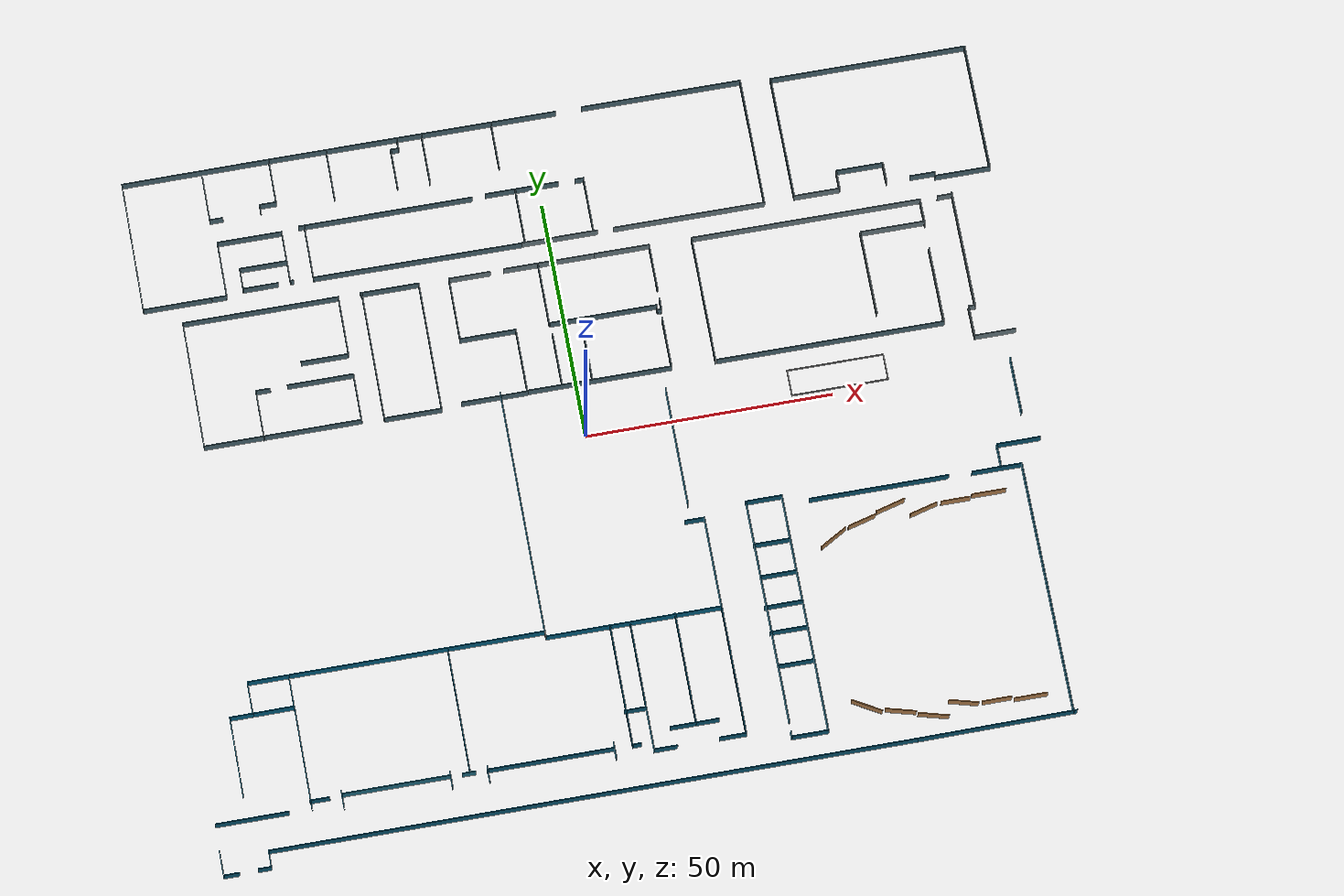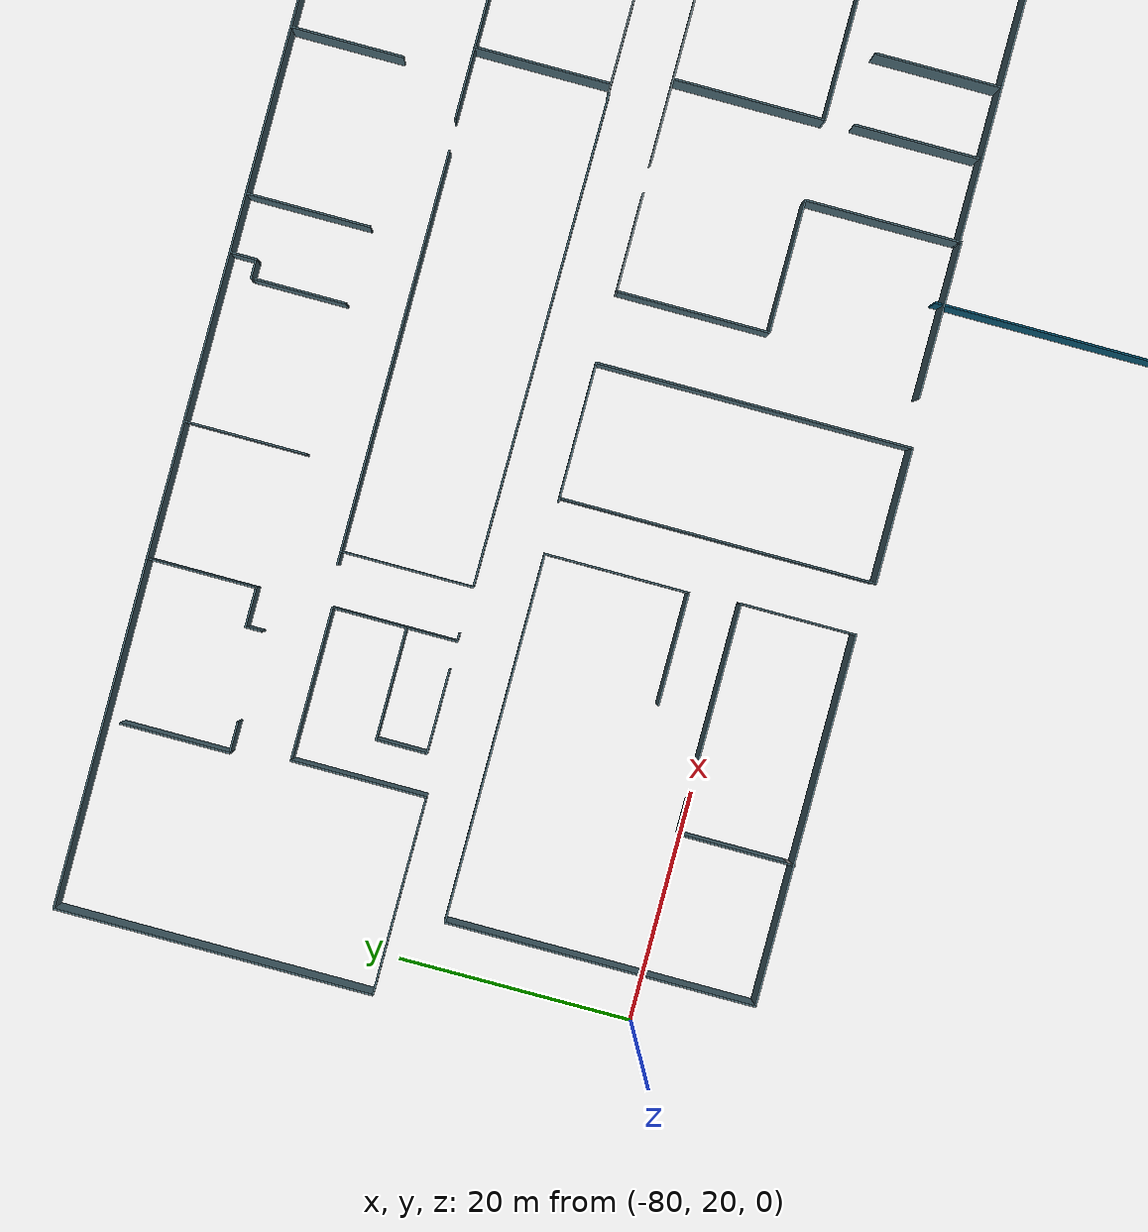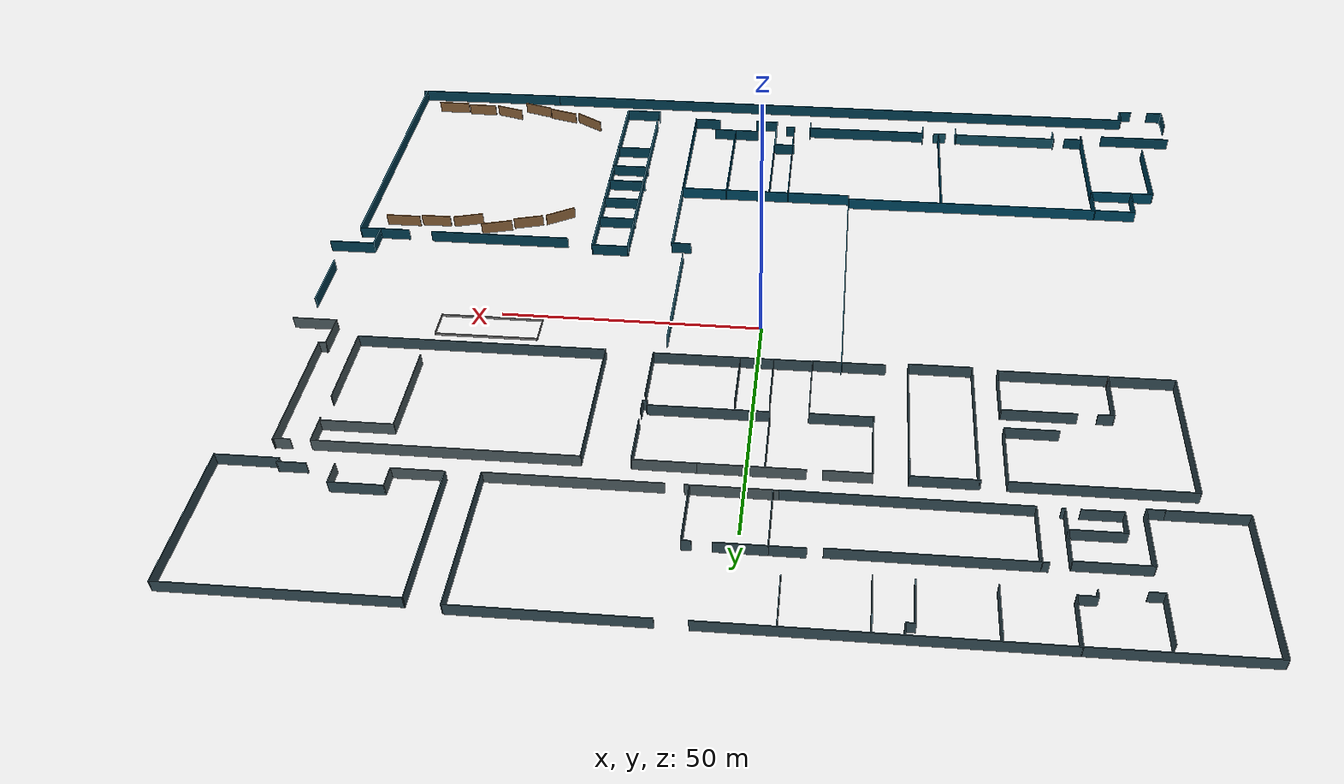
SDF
<?xml version='1.0'?>
<sdf version='1.6'>
  <model name='eceb'>
    <pose frame=''>2.10284 -4.41124 0 0 -0 0</pose>
    <link name='Wall_10'>
      <collision name='Wall_10_Collision'>
        <geometry>
          <box>
            <size>7.25 0.15 2.5</size>
          </box>
        </geometry>
        <pose frame=''>0 0 1.25 0 -0 0</pose>
      </collision>
      <visual name='Wall_10_Visual'>
        <pose frame=''>0 0 1.25 0 -0 0</pose>
        <geometry>
          <box>
            <size>7.25 0.15 2.5</size>
          </box>
        </geometry>
        <material>
          <script>
            <uri>file://media/materials/scripts/gazebo.material</uri>
            <name>Gazebo/Grey</name>
          </script>
          <ambient>0.282353 0.403922 0.447059 1</ambient>
        </material>
        <meta>
          <layer>0</layer>
        </meta>
      </visual>
      <pose frame=''>-61.0369 46.7249 0 0 -0 0</pose>
    </link>
    <link name='Wall_102'>
      <collision name='Wall_102_Collision'>
        <geometry>
          <box>
            <size>12 0.15 2.5</size>
          </box>
        </geometry>
        <pose frame=''>0 0 1.25 0 -0 0</pose>
      </collision>
      <visual name='Wall_102_Visual'>
        <pose frame=''>0 0 1.25 0 -0 0</pose>
        <geometry>
          <box>
            <size>12 0.15 2.5</size>
          </box>
        </geometry>
        <material>
          <script>
            <uri>file://media/materials/scripts/gazebo.material</uri>
            <name>Gazebo/Grey</name>
          </script>
          <ambient>0.282353 0.403922 0.447059 1</ambient>
        </material>
        <meta>
          <layer>0</layer>
        </meta>
      </visual>
      <pose frame=''>-35.6171 41.6407 0 0 -0 0</pose>
    </link>
    <link name='Wall_103'>
      <collision name='Wall_103_Collision'>
        <geometry>
          <box>
            <size>27.25 0.15 2.5</size>
          </box>
        </geometry>
        <pose frame=''>0 0 1.25 0 -0 0</pose>
      </collision>
      <visual name='Wall_103_Visual'>
        <pose frame=''>0 0 1.25 0 -0 0</pose>
        <geometry>
          <box>
            <size>27.25 0.15 2.5</size>
          </box>
        </geometry>
        <material>
          <script>
            <uri>file://media/materials/scripts/gazebo.material</uri>
            <name>Gazebo/Grey</name>
          </script>
          <ambient>0.282353 0.403922 0.447059 1</ambient>
        </material>
        <meta>
          <layer>0</layer>
        </meta>
      </visual>
      <pose frame=''>-29.6921 28.0907 0 0 -0 -1.5708</pose>
    </link>
    <link name='Wall_104'>
      <collision name='Wall_104_Collision'>
        <geometry>
          <box>
            <size>11.75 0.15 2.5</size>
          </box>
        </geometry>
        <pose frame=''>0 0 1.25 0 -0 0</pose>
      </collision>
      <visual name='Wall_104_Visual'>
        <pose frame=''>0 0 1.25 0 -0 0</pose>
        <geometry>
          <box>
            <size>11.75 0.15 2.5</size>
          </box>
        </geometry>
        <material>
          <script>
            <uri>file://media/materials/scripts/gazebo.material</uri>
            <name>Gazebo/Grey</name>
          </script>
          <ambient>0.282353 0.403922 0.447059 1</ambient>
        </material>
        <meta>
          <layer>0</layer>
        </meta>
      </visual>
      <pose frame=''>-35.4921 14.5407 0 0 -0 3.14159</pose>
    </link>
    <link name='Wall_105'>
      <collision name='Wall_105_Collision'>
        <geometry>
          <box>
            <size>27.25 0.15 2.5</size>
          </box>
        </geometry>
        <pose frame=''>0 0 1.25 0 -0 0</pose>
      </collision>
      <visual name='Wall_105_Visual'>
        <pose frame=''>0 0 1.25 0 -0 0</pose>
        <geometry>
          <box>
            <size>27.25 0.15 2.5</size>
          </box>
        </geometry>
        <material>
          <script>
            <uri>file://media/materials/scripts/gazebo.material</uri>
            <name>Gazebo/Grey</name>
          </script>
          <ambient>0.282353 0.403922 0.447059 1</ambient>
        </material>
        <meta>
          <layer>0</layer>
        </meta>
      </visual>
      <pose frame=''>-41.2921 28.0907 0 0 -0 1.5708</pose>
    </link>
    <link name='Wall_107'>
      <collision name='Wall_107_Collision'>
        <geometry>
          <box>
            <size>13.25 0.15 2.5</size>
          </box>
        </geometry>
        <pose frame=''>0 0 1.25 0 -0 0</pose>
      </collision>
      <visual name='Wall_107_Visual'>
        <pose frame=''>0 0 1.25 0 -0 0</pose>
        <geometry>
          <box>
            <size>13.25 0.15 2.5</size>
          </box>
        </geometry>
        <material>
          <script>
            <uri>file://media/materials/scripts/gazebo.material</uri>
            <name>Gazebo/Grey</name>
          </script>
          <ambient>0.282353 0.403922 0.447059 1</ambient>
        </material>
        <meta>
          <layer>0</layer>
        </meta>
      </visual>
      <pose frame=''>-23.5412 35.0069 0 0 -0 -1.5708</pose>
    </link>
    <link name='Wall_108'>
      <collision name='Wall_108_Collision'>
        <geometry>
          <box>
            <size>11.5 0.15 2.5</size>
          </box>
        </geometry>
        <pose frame=''>0 0 1.25 0 -0 0</pose>
      </collision>
      <visual name='Wall_108_Visual'>
        <pose frame=''>0 0 1.25 0 -0 0</pose>
        <geometry>
          <box>
            <size>11.5 0.15 2.5</size>
          </box>
        </geometry>
        <material>
          <script>
            <uri>file://media/materials/scripts/gazebo.material</uri>
            <name>Gazebo/Grey</name>
          </script>
          <ambient>0.282353 0.403922 0.447059 1</ambient>
        </material>
        <meta>
          <layer>0</layer>
        </meta>
      </visual>
      <pose frame=''>-17.8662 28.4569 0 0 -0 0</pose>
    </link>
    <link name='Wall_109'>
      <collision name='Wall_109_Collision'>
        <geometry>
          <box>
            <size>13.5 0.15 2.5</size>
          </box>
        </geometry>
        <pose frame=''>0 0 1.25 0 -0 0</pose>
      </collision>
      <visual name='Wall_109_Visual'>
        <pose frame=''>0 0 1.25 0 -0 0</pose>
        <geometry>
          <box>
            <size>13.5 0.15 2.5</size>
          </box>
        </geometry>
        <material>
          <script>
            <uri>file://media/materials/scripts/gazebo.material</uri>
            <name>Gazebo/Grey</name>
          </script>
          <ambient>0.282353 0.403922 0.447059 1</ambient>
        </material>
        <meta>
          <layer>0</layer>
        </meta>
      </visual>
      <pose frame=''>-12.1912 21.7819 0 0 -0 -1.5708</pose>
    </link>
    <link name='Wall_110'>
      <collision name='Wall_110_Collision'>
        <geometry>
          <box>
            <size>13.5 0.15 2.5</size>
          </box>
        </geometry>
        <pose frame=''>0 0 1.25 0 -0 0</pose>
      </collision>
      <visual name='Wall_110_Visual'>
        <pose frame=''>0 0 1.25 0 -0 0</pose>
        <geometry>
          <box>
            <size>13.5 0.15 2.5</size>
          </box>
        </geometry>
        <material>
          <script>
            <uri>file://media/materials/scripts/gazebo.material</uri>
            <name>Gazebo/Grey</name>
          </script>
          <ambient>0.282353 0.403922 0.447059 1</ambient>
        </material>
        <meta>
          <layer>0</layer>
        </meta>
      </visual>
      <pose frame=''>-18.8662 15.1069 0 0 -0 3.14159</pose>
    </link>
    <link name='Wall_112'>
      <collision name='Wall_112_Collision'>
        <geometry>
          <box>
            <size>8.5 0.15 2.5</size>
          </box>
        </geometry>
        <pose frame=''>0 0 1.25 0 -0 0</pose>
      </collision>
      <visual name='Wall_112_Visual'>
        <pose frame=''>0 0 1.25 0 -0 0</pose>
        <geometry>
          <box>
            <size>8.5 0.15 2.5</size>
          </box>
        </geometry>
        <material>
          <script>
            <uri>file://media/materials/scripts/gazebo.material</uri>
            <name>Gazebo/Grey</name>
          </script>
          <ambient>0.411765 0.486275 0.509804 1</ambient>
        </material>
        <meta>
          <layer>0</layer>
        </meta>
      </visual>
      <pose frame=''>-19.3662 41.557 0 0 -0 0</pose>
    </link>
    <link name='Wall_114'>
      <collision name='Wall_114_Collision'>
        <geometry>
          <box>
            <size>18.75 0.15 2.5</size>
          </box>
        </geometry>
        <pose frame=''>0 0 1.25 0 -0 0</pose>
      </collision>
      <visual name='Wall_114_Visual'>
        <pose frame=''>0 0 1.25 0 -0 0</pose>
        <geometry>
          <box>
            <size>18.75 0.15 2.5</size>
          </box>
        </geometry>
        <material>
          <script>
            <uri>file://media/materials/scripts/gazebo.material</uri>
            <name>Gazebo/Grey</name>
          </script>
          <ambient>0.411765 0.486275 0.509804 1</ambient>
        </material>
        <meta>
          <layer>0</layer>
        </meta>
      </visual>
      <pose frame=''>-3.06602 41.6234 0 0 -0 0</pose>
    </link>
    <link name='Wall_116'>
      <collision name='Wall_116_Collision'>
        <geometry>
          <box>
            <size>11.25 0.15 2.5</size>
          </box>
        </geometry>
        <pose frame=''>0 0 1.25 0 -0 0</pose>
      </collision>
      <visual name='Wall_116_Visual'>
        <pose frame=''>0 0 1.25 0 -0 0</pose>
        <geometry>
          <box>
            <size>11.25 0.15 2.5</size>
          </box>
        </geometry>
        <material>
          <script>
            <uri>file://media/materials/scripts/gazebo.material</uri>
            <name>Gazebo/Grey</name>
          </script>
          <ambient>0.411765 0.486275 0.509804 1</ambient>
        </material>
        <meta>
          <layer>0</layer>
        </meta>
      </visual>
      <pose frame=''>11.784 41.6234 0 0 -0 0</pose>
    </link>
    <link name='Wall_117'>
      <collision name='Wall_117_Collision'>
        <geometry>
          <box>
            <size>9.5 0.15 2.5</size>
          </box>
        </geometry>
        <pose frame=''>0 0 1.25 0 -0 0</pose>
      </collision>
      <visual name='Wall_117_Visual'>
        <pose frame=''>0 0 1.25 0 -0 0</pose>
        <geometry>
          <box>
            <size>9.5 0.15 2.5</size>
          </box>
        </geometry>
        <material>
          <script>
            <uri>file://media/materials/scripts/gazebo.material</uri>
            <name>Gazebo/Grey</name>
          </script>
          <ambient>0.282353 0.403922 0.447059 1</ambient>
        </material>
        <meta>
          <layer>0</layer>
        </meta>
      </visual>
      <pose frame=''>17.334 36.9484 0 0 -0 -1.5708</pose>
    </link>
    <link name='Wall_119'>
      <collision name='Wall_119_Collision'>
        <geometry>
          <box>
            <size>2.5 0.15 2.5</size>
          </box>
        </geometry>
        <pose frame=''>0 0 1.25 0 -0 0</pose>
      </collision>
      <visual name='Wall_119_Visual'>
        <pose frame=''>0 0 1.25 0 -0 0</pose>
        <geometry>
          <box>
            <size>2.5 0.15 2.5</size>
          </box>
        </geometry>
        <material>
          <script>
            <uri>file://media/materials/scripts/gazebo.material</uri>
            <name>Gazebo/Grey</name>
          </script>
          <ambient>0.282353 0.403922 0.447059 1</ambient>
        </material>
        <meta>
          <layer>0</layer>
        </meta>
      </visual>
      <pose frame=''>17.3382 28.6905 0 0 -0 -1.5708</pose>
    </link>
    <link name='Wall_12'>
      <collision name='Wall_12_Collision'>
        <geometry>
          <box>
            <size>4.5 0.15 2.5</size>
          </box>
        </geometry>
        <pose frame=''>0 0 1.25 0 -0 0</pose>
      </collision>
      <visual name='Wall_12_Visual'>
        <pose frame=''>0 0 1.25 0 -0 0</pose>
        <geometry>
          <box>
            <size>4.5 0.15 2.5</size>
          </box>
        </geometry>
        <material>
          <script>
            <uri>file://media/materials/scripts/gazebo.material</uri>
            <name>Gazebo/Grey</name>
          </script>
          <ambient>0.282353 0.403922 0.447059 1</ambient>
        </material>
        <meta>
          <layer>0</layer>
        </meta>
      </visual>
      <pose frame=''>-54.9869 48.8998 0 0 -0 -1.5708</pose>
    </link>
    <link name='Wall_121'>
      <collision name='Wall_121_Collision'>
        <geometry>
          <box>
            <size>1 0.15 2.5</size>
          </box>
        </geometry>
        <pose frame=''>0 0 1.25 0 -0 0</pose>
      </collision>
      <visual name='Wall_121_Visual'>
        <pose frame=''>0 0 1.25 0 -0 0</pose>
        <geometry>
          <box>
            <size>1 0.15 2.5</size>
          </box>
        </geometry>
        <material>
          <script>
            <uri>file://media/materials/scripts/gazebo.material</uri>
            <name>Gazebo/Grey</name>
          </script>
          <ambient>0.282353 0.403922 0.447059 1</ambient>
        </material>
        <meta>
          <layer>0</layer>
        </meta>
      </visual>
      <pose frame=''>16.9132 27.5155 0 0 -0 3.14159</pose>
    </link>
    <link name='Wall_122'>
      <collision name='Wall_122_Collision'>
        <geometry>
          <box>
            <size>1.25 0.15 2.5</size>
          </box>
        </geometry>
        <pose frame=''>0 0 1.25 0 -0 0</pose>
      </collision>
      <visual name='Wall_122_Visual'>
        <pose frame=''>0 0 1.25 0 -0 0</pose>
        <geometry>
          <box>
            <size>1.25 0.15 2.5</size>
          </box>
        </geometry>
        <material>
          <script>
            <uri>file://media/materials/scripts/gazebo.material</uri>
            <name>Gazebo/Grey</name>
          </script>
          <ambient>0.282353 0.403922 0.447059 1</ambient>
        </material>
        <meta>
          <layer>0</layer>
        </meta>
      </visual>
      <pose frame=''>16.4882 28.0655 0 0 -0 1.5708</pose>
    </link>
    <link name='Wall_123'>
      <collision name='Wall_123_Collision'>
        <geometry>
          <box>
            <size>22 0.15 2.5</size>
          </box>
        </geometry>
        <pose frame=''>0 0 1.25 0 -0 0</pose>
      </collision>
      <visual name='Wall_123_Visual'>
        <pose frame=''>0 0 1.25 0 -0 0</pose>
        <geometry>
          <box>
            <size>22 0.15 2.5</size>
          </box>
        </geometry>
        <material>
          <script>
            <uri>file://media/materials/scripts/gazebo.material</uri>
            <name>Gazebo/Grey</name>
          </script>
          <ambient>0.282353 0.403922 0.447059 1</ambient>
        </material>
        <meta>
          <layer>0</layer>
        </meta>
      </visual>
      <pose frame=''>5.5632 28.6155 0 0 -0 3.14159</pose>
    </link>
    <link name='Wall_124'>
      <collision name='Wall_124_Collision'>
        <geometry>
          <box>
            <size>13 0.15 2.5</size>
          </box>
        </geometry>
        <pose frame=''>0 0 1.25 0 -0 0</pose>
      </collision>
      <visual name='Wall_124_Visual'>
        <pose frame=''>0 0 1.25 0 -0 0</pose>
        <geometry>
          <box>
            <size>13 0.15 2.5</size>
          </box>
        </geometry>
        <material>
          <script>
            <uri>file://media/materials/scripts/gazebo.material</uri>
            <name>Gazebo/Grey</name>
          </script>
          <ambient>0.282353 0.403922 0.447059 1</ambient>
        </material>
        <meta>
          <layer>0</layer>
        </meta>
      </visual>
      <pose frame=''>-5.3618 35.0405 0 0 -0 1.5708</pose>
    </link>
    <link name='Wall_126'>
      <collision name='Wall_126_Collision'>
        <geometry>
          <box>
            <size>10.75 0.15 2.5</size>
          </box>
        </geometry>
        <pose frame=''>0 0 1.25 0 -0 0</pose>
      </collision>
      <visual name='Wall_126_Visual'>
        <pose frame=''>0 0 1.25 0 -0 0</pose>
        <geometry>
          <box>
            <size>10.75 0.15 2.5</size>
          </box>
        </geometry>
        <material>
          <script>
            <uri>file://media/materials/scripts/gazebo.material</uri>
            <name>Gazebo/Grey</name>
          </script>
          <ambient>0.282353 0.403922 0.447059 1</ambient>
        </material>
        <meta>
          <layer>0</layer>
        </meta>
      </visual>
      <pose frame=''>17.1199 20.5308 0 0 -0 -1.5708</pose>
    </link>
    <link name='Wall_127'>
      <collision name='Wall_127_Collision'>
        <geometry>
          <box>
            <size>29.5 0.15 2.5</size>
          </box>
        </geometry>
        <pose frame=''>0 0 1.25 0 -0 0</pose>
      </collision>
      <visual name='Wall_127_Visual'>
        <pose frame=''>0 0 1.25 0 -0 0</pose>
        <geometry>
          <box>
            <size>29.5 0.15 2.5</size>
          </box>
        </geometry>
        <material>
          <script>
            <uri>file://media/materials/scripts/gazebo.material</uri>
            <name>Gazebo/Grey</name>
          </script>
          <ambient>0.282353 0.403922 0.447059 1</ambient>
        </material>
        <meta>
          <layer>0</layer>
        </meta>
      </visual>
      <pose frame=''>2.44485 15.2308 0 0 -0 3.14159</pose>
    </link>
    <link name='Wall_129'>
      <collision name='Wall_129_Collision'>
        <geometry>
          <box>
            <size>10.75 0.15 2.5</size>
          </box>
        </geometry>
        <pose frame=''>0 0 1.25 0 -0 0</pose>
      </collision>
      <visual name='Wall_129_Visual'>
        <pose frame=''>0 0 1.25 0 -0 0</pose>
        <geometry>
          <box>
            <size>10.75 0.15 2.5</size>
          </box>
        </geometry>
        <material>
          <script>
            <uri>file://media/materials/scripts/gazebo.material</uri>
            <name>Gazebo/Grey</name>
          </script>
          <ambient>0.282353 0.403922 0.447059 1</ambient>
        </material>
        <meta>
          <layer>0</layer>
        </meta>
      </visual>
      <pose frame=''>1.04463 20.6982 0 0 -0 -1.5708</pose>
    </link>
    <link name='Wall_13'>
      <collision name='Wall_13_Collision'>
        <geometry>
          <box>
            <size>0.75 0.15 2.5</size>
          </box>
        </geometry>
        <pose frame=''>0 0 1.25 0 -0 0</pose>
      </collision>
      <visual name='Wall_13_Visual'>
        <pose frame=''>0 0 1.25 0 -0 0</pose>
        <geometry>
          <box>
            <size>0.75 0.15 2.5</size>
          </box>
        </geometry>
        <material>
          <script>
            <uri>file://media/materials/scripts/gazebo.material</uri>
            <name>Gazebo/Grey</name>
          </script>
          <ambient>0.282353 0.403922 0.447059 1</ambient>
        </material>
        <meta>
          <layer>0</layer>
        </meta>
      </visual>
      <pose frame=''>-54.6869 46.7249 0 0 -0 0</pose>
    </link>
    <link name='Wall_131'>
      <collision name='Wall_131_Collision'>
        <geometry>
          <box>
            <size>10.75 0.15 2.5</size>
          </box>
        </geometry>
        <pose frame=''>0 0 1.25 0 -0 0</pose>
      </collision>
      <visual name='Wall_131_Visual'>
        <pose frame=''>0 0 1.25 0 -0 0</pose>
        <geometry>
          <box>
            <size>10.75 0.15 2.5</size>
          </box>
        </geometry>
        <material>
          <script>
            <uri>file://media/materials/scripts/gazebo.material</uri>
            <name>Gazebo/Grey</name>
          </script>
          <ambient>0.282353 0.403922 0.447059 1</ambient>
        </material>
        <meta>
          <layer>0</layer>
        </meta>
      </visual>
      <pose frame=''>-5.10917 20.8238 0 0 -0 -1.5708</pose>
    </link>
    <link name='Wall_134'>
      <collision name='Wall_134_Collision'>
        <geometry>
          <box>
            <size>51 0.15 2.5</size>
          </box>
        </geometry>
        <pose frame=''>0 0 1.25 0 -0 0</pose>
      </collision>
      <visual name='Wall_134_Visual'>
        <pose frame=''>0 0 1.25 0 -0 0</pose>
        <geometry>
          <box>
            <size>51 0.15 2.5</size>
          </box>
        </geometry>
        <material>
          <script>
            <uri>file://media/materials/scripts/gazebo.material</uri>
            <name>Gazebo/Grey</name>
          </script>
          <ambient>0.0313726 0.333333 0.443137 1</ambient>
        </material>
        <meta>
          <layer>0</layer>
        </meta>
      </visual>
      <pose frame=''>-17.5625 -9.64396 0 0 -0 -1.5708</pose>
    </link>
    <link name='Wall_135'>
      <collision name='Wall_135_Collision'>
        <geometry>
          <box>
            <size>59.75 0.15 2.5</size>
          </box>
        </geometry>
        <pose frame=''>0 0 1.25 0 -0 0</pose>
      </collision>
      <visual name='Wall_135_Visual'>
        <pose frame=''>0 0 1.25 0 -0 0</pose>
        <geometry>
          <box>
            <size>59.75 0.15 2.5</size>
          </box>
        </geometry>
        <material>
          <script>
            <uri>file://media/materials/scripts/gazebo.material</uri>
            <name>Gazebo/Grey</name>
          </script>
          <ambient>0.00784314 0.372549 0.505882 1</ambient>
        </material>
        <meta>
          <layer>0</layer>
        </meta>
      </visual>
      <pose frame=''>-47.3625 -35.069 0 0 -0 3.14159</pose>
    </link>
    <link name='Wall_137'>
      <collision name='Wall_137_Collision'>
        <geometry>
          <box>
            <size>6.75 0.15 2.5</size>
          </box>
        </geometry>
        <pose frame=''>0 0 1.25 0 -0 0</pose>
      </collision>
      <visual name='Wall_137_Visual'>
        <pose frame=''>0 0 1.25 0 -0 0</pose>
        <geometry>
          <box>
            <size>6.75 0.15 2.5</size>
          </box>
        </geometry>
        <material>
          <script>
            <uri>file://media/materials/scripts/gazebo.material</uri>
            <name>Gazebo/Grey</name>
          </script>
          <ambient>0.00784314 0.372549 0.505882 1</ambient>
        </material>
        <meta>
          <layer>0</layer>
        </meta>
      </visual>
      <pose frame=''>-77.1625 -38.369 0 0 -0 -1.5708</pose>
    </link>
    <link name='Wall_138'>
      <collision name='Wall_138_Collision'>
        <geometry>
          <box>
            <size>4.75 0.15 2.5</size>
          </box>
        </geometry>
        <pose frame=''>0 0 1.25 0 -0 0</pose>
      </collision>
      <visual name='Wall_138_Visual'>
        <pose frame=''>0 0 1.25 0 -0 0</pose>
        <geometry>
          <box>
            <size>4.75 0.15 2.5</size>
          </box>
        </geometry>
        <material>
          <script>
            <uri>file://media/materials/scripts/gazebo.material</uri>
            <name>Gazebo/Grey</name>
          </script>
          <ambient>0.00784314 0.372549 0.505882 1</ambient>
        </material>
        <meta>
          <layer>0</layer>
        </meta>
      </visual>
      <pose frame=''>-79.4625 -41.669 0 0 -0 3.14159</pose>
    </link>
    <link name='Wall_139'>
      <collision name='Wall_139_Collision'>
        <geometry>
          <box>
            <size>16.5 0.15 2.5</size>
          </box>
        </geometry>
        <pose frame=''>0 0 1.25 0 -0 0</pose>
      </collision>
      <visual name='Wall_139_Visual'>
        <pose frame=''>0 0 1.25 0 -0 0</pose>
        <geometry>
          <box>
            <size>16.5 0.15 2.5</size>
          </box>
        </geometry>
        <material>
          <script>
            <uri>file://media/materials/scripts/gazebo.material</uri>
            <name>Gazebo/Grey</name>
          </script>
          <ambient>0.00784314 0.372549 0.505882 1</ambient>
        </material>
        <meta>
          <layer>0</layer>
        </meta>
      </visual>
      <pose frame=''>-81.7625 -49.844 0 0 -0 -1.5708</pose>
    </link>
    <link name='Wall_141'>
      <collision name='Wall_141_Collision'>
        <geometry>
          <box>
            <size>14.75 0.15 2.5</size>
          </box>
        </geometry>
        <pose frame=''>0 0 1.25 0 -0 0</pose>
      </collision>
      <visual name='Wall_141_Visual'>
        <pose frame=''>0 0 1.25 0 -0 0</pose>
        <geometry>
          <box>
            <size>14.75 0.15 2.5</size>
          </box>
        </geometry>
        <material>
          <script>
            <uri>file://media/materials/scripts/gazebo.material</uri>
            <name>Gazebo/Grey</name>
          </script>
          <ambient>0.0313726 0.333333 0.443137 1</ambient>
        </material>
        <meta>
          <layer>0</layer>
        </meta>
      </visual>
      <pose frame=''>-80.7569 -62.752 0 0 -0 0</pose>
    </link>
    <link name='Wall_143'>
      <collision name='Wall_143_Collision'>
        <geometry>
          <box>
            <size>5.25 0.15 2.5</size>
          </box>
        </geometry>
        <pose frame=''>0 0 1.25 0 -0 0</pose>
      </collision>
      <visual name='Wall_143_Visual'>
        <pose frame=''>0 0 1.25 0 -0 0</pose>
        <geometry>
          <box>
            <size>5.25 0.15 2.5</size>
          </box>
        </geometry>
        <material>
          <script>
            <uri>file://media/materials/scripts/gazebo.material</uri>
            <name>Gazebo/Grey</name>
          </script>
          <ambient>0.0313726 0.333333 0.443137 1</ambient>
        </material>
        <meta>
          <layer>0</layer>
        </meta>
      </visual>
      <pose frame=''>-88.1514 -70.7787 0 0 -0 -1.5708</pose>
    </link>
    <link name='Wall_144'>
      <collision name='Wall_144_Collision'>
        <geometry>
          <box>
            <size>3.25 0.15 2.5</size>
          </box>
        </geometry>
        <pose frame=''>0 0 1.25 0 -0 0</pose>
      </collision>
      <visual name='Wall_144_Visual'>
        <pose frame=''>0 0 1.25 0 -0 0</pose>
        <geometry>
          <box>
            <size>3.25 0.15 2.5</size>
          </box>
        </geometry>
        <material>
          <script>
            <uri>file://media/materials/scripts/gazebo.material</uri>
            <name>Gazebo/Grey</name>
          </script>
          <ambient>0.0313726 0.333333 0.443137 1</ambient>
        </material>
        <meta>
          <layer>0</layer>
        </meta>
      </visual>
      <pose frame=''>-86.6014 -73.3287 0 0 -0 0</pose>
    </link>
    <link name='Wall_146'>
      <collision name='Wall_146_Collision'>
        <geometry>
          <box>
            <size>2.75 0.15 2.5</size>
          </box>
        </geometry>
        <pose frame=''>0 0 1.25 0 -0 0</pose>
      </collision>
      <visual name='Wall_146_Visual'>
        <pose frame=''>0 0 1.25 0 -0 0</pose>
        <geometry>
          <box>
            <size>2.75 0.15 2.5</size>
          </box>
        </geometry>
        <material>
          <script>
            <uri>file://media/materials/scripts/gazebo.material</uri>
            <name>Gazebo/Grey</name>
          </script>
          <ambient>0.0313726 0.333333 0.443137 1</ambient>
        </material>
        <meta>
          <layer>0</layer>
        </meta>
      </visual>
      <pose frame=''>-79.9583 -73.2333 0 0 -0 0</pose>
    </link>
    <link name='Wall_147'>
      <collision name='Wall_147_Collision'>
        <geometry>
          <box>
            <size>3.5 0.15 2.5</size>
          </box>
        </geometry>
        <pose frame=''>0 0 1.25 0 -0 0</pose>
      </collision>
      <visual name='Wall_147_Visual'>
        <pose frame=''>0 0 1.25 0 -0 0</pose>
        <geometry>
          <box>
            <size>3.5 0.15 2.5</size>
          </box>
        </geometry>
        <material>
          <script>
            <uri>file://media/materials/scripts/gazebo.material</uri>
            <name>Gazebo/Grey</name>
          </script>
          <ambient>0.0313726 0.333333 0.443137 1</ambient>
        </material>
        <meta>
          <layer>0</layer>
        </meta>
      </visual>
      <pose frame=''>-78.6583 -71.5583 0 0 -0 1.5708</pose>
    </link>
    <link name='Wall_148'>
      <collision name='Wall_148_Collision'>
        <geometry>
          <box>
            <size>129.5 0.15 2.5</size>
          </box>
        </geometry>
        <pose frame=''>0 0 1.25 0 -0 0</pose>
      </collision>
      <visual name='Wall_148_Visual'>
        <pose frame=''>0 0 1.25 0 -0 0</pose>
        <geometry>
          <box>
            <size>129.5 0.15 2.5</size>
          </box>
        </geometry>
        <material>
          <script>
            <uri>file://media/materials/scripts/gazebo.material</uri>
            <name>Gazebo/Grey</name>
          </script>
          <ambient>0.0313726 0.333333 0.443137 1</ambient>
        </material>
        <meta>
          <layer>0</layer>
        </meta>
      </visual>
      <pose frame=''>-13.9833 -69.8833 0 0 -0 0</pose>
    </link>
    <link name='Wall_15'>
      <collision name='Wall_15_Collision'>
        <geometry>
          <box>
            <size>1.25 0.15 2.5</size>
          </box>
        </geometry>
        <pose frame=''>0 0 1.25 0 -0 0</pose>
      </collision>
      <visual name='Wall_15_Visual'>
        <pose frame=''>0 0 1.25 0 -0 0</pose>
        <geometry>
          <box>
            <size>1.25 0.15 2.5</size>
          </box>
        </geometry>
        <material>
          <script>
            <uri>file://media/materials/scripts/gazebo.material</uri>
            <name>Gazebo/Grey</name>
          </script>
          <ambient>0.282353 0.403922 0.447059 1</ambient>
        </material>
        <meta>
          <layer>0</layer>
        </meta>
      </visual>
      <pose frame=''>-50.8487 57.9626 0 0 -0 0</pose>
    </link>
    <link name='Wall_151'>
      <collision name='Wall_151_Collision'>
        <geometry>
          <box>
            <size>32.09 0.15 2.5</size>
          </box>
        </geometry>
        <pose frame=''>0 0 1.25 0 -0 0</pose>
      </collision>
      <visual name='Wall_151_Visual'>
        <pose frame=''>0 0 1.25 0 -0 0</pose>
        <geometry>
          <box>
            <size>32.09 0.15 2.5</size>
          </box>
        </geometry>
        <material>
          <script>
            <uri>file://media/materials/scripts/gazebo.material</uri>
            <name>Gazebo/Grey</name>
          </script>
          <ambient>0.0313726 0.333333 0.443137 1</ambient>
        </material>
        <meta>
          <layer>0</layer>
        </meta>
      </visual>
      <pose frame=''>66.8099 -69.7617 0 0 -0 -3.13376</pose>
    </link>
    <link name='Wall_156'>
      <collision name='Wall_156_Collision'>
        <geometry>
          <box>
            <size>21.25 0.15 2.5</size>
          </box>
        </geometry>
        <pose frame=''>0 0 1.25 0 -0 0</pose>
      </collision>
      <visual name='Wall_156_Visual'>
        <pose frame=''>0 0 1.25 0 -0 0</pose>
        <geometry>
          <box>
            <size>21.25 0.15 2.5</size>
          </box>
        </geometry>
        <material>
          <script>
            <uri>file://media/materials/scripts/gazebo.material</uri>
            <name>Gazebo/Grey</name>
          </script>
          <ambient>0.00784314 0.372549 0.505882 1</ambient>
        </material>
        <meta>
          <layer>0</layer>
        </meta>
      </visual>
      <pose frame=''>-68.8592 -52.1746 0 0 -0 1.5708</pose>
    </link>
    <link name='Wall_157'>
      <collision name='Wall_157_Collision'>
        <geometry>
          <box>
            <size>8.4534 0.15 2.5</size>
          </box>
        </geometry>
        <pose frame=''>0 0 1.25 0 -0 0</pose>
      </collision>
      <visual name='Wall_157_Visual'>
        <pose frame=''>0 0 1.25 0 -0 0</pose>
        <geometry>
          <box>
            <size>8.4534 0.15 2.5</size>
          </box>
        </geometry>
        <material>
          <script>
            <uri>file://media/materials/scripts/gazebo.material</uri>
            <name>Gazebo/Grey</name>
          </script>
          <ambient>0.00784314 0.372549 0.505882 1</ambient>
        </material>
        <meta>
          <layer>0</layer>
        </meta>
      </visual>
      <pose frame=''>-73.0109 -41.6468 0 0 -0 -3.13625</pose>
    </link>
    <link name='Wall_159'>
      <collision name='Wall_159_Collision'>
        <geometry>
          <box>
            <size>7 0.15 2.5</size>
          </box>
        </geometry>
        <pose frame=''>0 0 1.25 0 -0 0</pose>
      </collision>
      <visual name='Wall_159_Visual'>
        <pose frame=''>0 0 1.25 0 -0 0</pose>
        <geometry>
          <box>
            <size>7 0.15 2.5</size>
          </box>
        </geometry>
        <material>
          <script>
            <uri>file://media/materials/scripts/gazebo.material</uri>
            <name>Gazebo/Grey</name>
          </script>
          <ambient>0.00784314 0.372549 0.505882 1</ambient>
        </material>
        <meta>
          <layer>0</layer>
        </meta>
      </visual>
      <pose frame=''>-68.9119 -38.4042 0 0 -0 -1.5708</pose>
    </link>
    <link name='Wall_16'>
      <collision name='Wall_16_Collision'>
        <geometry>
          <box>
            <size>11.5 0.15 2.5</size>
          </box>
        </geometry>
        <pose frame=''>0 0 1.25 0 -0 0</pose>
      </collision>
      <visual name='Wall_16_Visual'>
        <pose frame=''>0 0 1.25 0 -0 0</pose>
        <geometry>
          <box>
            <size>11.5 0.15 2.5</size>
          </box>
        </geometry>
        <material>
          <script>
            <uri>file://media/materials/scripts/gazebo.material</uri>
            <name>Gazebo/Grey</name>
          </script>
          <ambient>0.282353 0.403922 0.447059 1</ambient>
        </material>
        <meta>
          <layer>0</layer>
        </meta>
      </visual>
      <pose frame=''>-50.2987 52.2876 0 0 -0 -1.5708</pose>
    </link>
    <link name='Wall_161'>
      <collision name='Wall_161_Collision'>
        <geometry>
          <box>
            <size>4 0.15 2.5</size>
          </box>
        </geometry>
        <pose frame=''>0 0 1.25 0 -0 0</pose>
      </collision>
      <visual name='Wall_161_Visual'>
        <pose frame=''>0 0 1.25 0 -0 0</pose>
        <geometry>
          <box>
            <size>4 0.15 2.5</size>
          </box>
        </geometry>
        <material>
          <script>
            <uri>file://media/materials/scripts/gazebo.material</uri>
            <name>Gazebo/Grey</name>
          </script>
          <ambient>0.0313726 0.333333 0.443137 1</ambient>
        </material>
        <meta>
          <layer>0</layer>
        </meta>
      </visual>
      <pose frame=''>-67.0768 -61.2451 0 0 -0 3.14159</pose>
    </link>
    <link name='Wall_163'>
      <collision name='Wall_163_Collision'>
        <geometry>
          <box>
            <size>3.5 0.15 2.5</size>
          </box>
        </geometry>
        <pose frame=''>0 0 1.25 0 -0 0</pose>
      </collision>
      <visual name='Wall_163_Visual'>
        <pose frame=''>0 0 1.25 0 -0 0</pose>
        <geometry>
          <box>
            <size>3.5 0.15 2.5</size>
          </box>
        </geometry>
        <material>
          <script>
            <uri>file://media/materials/scripts/gazebo.material</uri>
            <name>Gazebo/Grey</name>
          </script>
          <ambient>0.0313726 0.333333 0.443137 1</ambient>
        </material>
        <meta>
          <layer>0</layer>
        </meta>
      </visual>
      <pose frame=''>-62.6452 -62.0149 0 0 -0 -1.5708</pose>
    </link>
    <link name='Wall_166'>
      <collision name='Wall_166_Collision'>
        <geometry>
          <box>
            <size>21.5 0.15 2.5</size>
          </box>
        </geometry>
        <pose frame=''>0 0 1.25 0 -0 0</pose>
      </collision>
      <visual name='Wall_166_Visual'>
        <pose frame=''>0 0 1.25 0 -0 0</pose>
        <geometry>
          <box>
            <size>21.5 0.15 2.5</size>
          </box>
        </geometry>
        <material>
          <script>
            <uri>file://media/materials/scripts/gazebo.material</uri>
            <name>Gazebo/Grey</name>
          </script>
          <ambient>0.109804 0.415686 0.505882 1</ambient>
        </material>
        <meta>
          <layer>0</layer>
        </meta>
      </visual>
      <pose frame=''>-51.8547 -61.0074 0 0 -0 0</pose>
    </link>
    <link name='Wall_168'>
      <collision name='Wall_168_Collision'>
        <geometry>
          <box>
            <size>3.25 0.15 2.5</size>
          </box>
        </geometry>
        <pose frame=''>0 0 1.25 0 -0 0</pose>
      </collision>
      <visual name='Wall_168_Visual'>
        <pose frame=''>0 0 1.25 0 -0 0</pose>
        <geometry>
          <box>
            <size>3.25 0.15 2.5</size>
          </box>
        </geometry>
        <material>
          <script>
            <uri>file://media/materials/scripts/gazebo.material</uri>
            <name>Gazebo/Grey</name>
          </script>
          <ambient>0.0313726 0.333333 0.443137 1</ambient>
        </material>
        <meta>
          <layer>0</layer>
        </meta>
      </visual>
      <pose frame=''>-40.9887 -61.8787 0 0 -0 -1.5708</pose>
    </link>
    <link name='Wall_17'>
      <collision name='Wall_17_Collision'>
        <geometry>
          <box>
            <size>42.5 0.15 2.5</size>
          </box>
        </geometry>
        <pose frame=''>0 0 1.25 0 -0 0</pose>
      </collision>
      <visual name='Wall_17_Visual'>
        <pose frame=''>0 0 1.25 0 -0 0</pose>
        <geometry>
          <box>
            <size>42.5 0.15 2.5</size>
          </box>
        </geometry>
        <material>
          <script>
            <uri>file://media/materials/scripts/gazebo.material</uri>
            <name>Gazebo/Grey</name>
          </script>
          <ambient>0.282353 0.403922 0.447059 1</ambient>
        </material>
        <meta>
          <layer>0</layer>
        </meta>
      </visual>
      <pose frame=''>-29.1237 46.5292 0 0 -0 -0.00394</pose>
    </link>
    <link name='Wall_170'>
      <collision name='Wall_170_Collision'>
        <geometry>
          <box>
            <size>2.75 0.15 2.5</size>
          </box>
        </geometry>
        <pose frame=''>0 0 1.25 0 -0 0</pose>
      </collision>
      <visual name='Wall_170_Visual'>
        <pose frame=''>0 0 1.25 0 -0 0</pose>
        <geometry>
          <box>
            <size>2.75 0.15 2.5</size>
          </box>
        </geometry>
        <material>
          <script>
            <uri>file://media/materials/scripts/gazebo.material</uri>
            <name>Gazebo/Grey</name>
          </script>
          <ambient>0.109804 0.415686 0.505882 1</ambient>
        </material>
        <meta>
          <layer>0</layer>
        </meta>
      </visual>
      <pose frame=''>-37.3257 -61.0997 0 0 -0 0</pose>
    </link>
    <link name='Wall_172'>
      <collision name='Wall_172_Collision'>
        <geometry>
          <box>
            <size>26 0.15 2.5</size>
          </box>
        </geometry>
        <pose frame=''>0 0 1.25 0 -0 0</pose>
      </collision>
      <visual name='Wall_172_Visual'>
        <pose frame=''>0 0 1.25 0 -0 0</pose>
        <geometry>
          <box>
            <size>26 0.15 2.5</size>
          </box>
        </geometry>
        <material>
          <script>
            <uri>file://media/materials/scripts/gazebo.material</uri>
            <name>Gazebo/Grey</name>
          </script>
          <ambient>0.00784314 0.372549 0.505882 1</ambient>
        </material>
        <meta>
          <layer>0</layer>
        </meta>
      </visual>
      <pose frame=''>-37.0975 -48.0841 0 0 -0 -1.5708</pose>
    </link>
    <link name='Wall_177'>
      <collision name='Wall_177_Collision'>
        <geometry>
          <box>
            <size>1.25 0.15 2.5</size>
          </box>
        </geometry>
        <pose frame=''>0 0 1.25 0 -0 0</pose>
      </collision>
      <visual name='Wall_177_Visual'>
        <pose frame=''>0 0 1.25 0 -0 0</pose>
        <geometry>
          <box>
            <size>1.25 0.15 2.5</size>
          </box>
        </geometry>
        <material>
          <script>
            <uri>file://media/materials/scripts/gazebo.material</uri>
            <name>Gazebo/Grey</name>
          </script>
          <ambient>1 1 1 1</ambient>
        </material>
        <meta>
          <layer>0</layer>
        </meta>
      </visual>
      <pose frame=''>-17.5625 -35.619 0 0 -0 -1.5708</pose>
    </link>
    <link name='Wall_178'>
      <collision name='Wall_178_Collision'>
        <geometry>
          <box>
            <size>35.5 0.15 2.5</size>
          </box>
        </geometry>
        <pose frame=''>0 0 1.25 0 -0 0</pose>
      </collision>
      <visual name='Wall_178_Visual'>
        <pose frame=''>0 0 1.25 0 -0 0</pose>
        <geometry>
          <box>
            <size>35.5 0.15 2.5</size>
          </box>
        </geometry>
        <material>
          <script>
            <uri>file://media/materials/scripts/gazebo.material</uri>
            <name>Gazebo/Grey</name>
          </script>
          <ambient>0.00784314 0.372549 0.505882 1</ambient>
        </material>
        <meta>
          <layer>0</layer>
        </meta>
      </visual>
      <pose frame=''>0.112491 -36.169 0 0 -0 0</pose>
    </link>
    <link name='Wall_180'>
      <collision name='Wall_180_Collision'>
        <geometry>
          <box>
            <size>3.25 0.15 2.5</size>
          </box>
        </geometry>
        <pose frame=''>0 0 1.25 0 -0 0</pose>
      </collision>
      <visual name='Wall_180_Visual'>
        <pose frame=''>0 0 1.25 0 -0 0</pose>
        <geometry>
          <box>
            <size>3.25 0.15 2.5</size>
          </box>
        </geometry>
        <material>
          <script>
            <uri>file://media/materials/scripts/gazebo.material</uri>
            <name>Gazebo/Grey</name>
          </script>
          <ambient>0.0313726 0.333333 0.443137 1</ambient>
        </material>
        <meta>
          <layer>0</layer>
        </meta>
      </visual>
      <pose frame=''>-33.5892 -61.8114 0 0 -0 -1.5708</pose>
    </link>
    <link name='Wall_182'>
      <collision name='Wall_182_Collision'>
        <geometry>
          <box>
            <size>25.5 0.15 2.5</size>
          </box>
        </geometry>
        <pose frame=''>0 0 1.25 0 -0 0</pose>
      </collision>
      <visual name='Wall_182_Visual'>
        <pose frame=''>0 0 1.25 0 -0 0</pose>
        <geometry>
          <box>
            <size>25.5 0.15 2.5</size>
          </box>
        </geometry>
        <material>
          <script>
            <uri>file://media/materials/scripts/gazebo.material</uri>
            <name>Gazebo/Grey</name>
          </script>
          <ambient>0.0313726 0.333333 0.443137 1</ambient>
        </material>
        <meta>
          <layer>0</layer>
        </meta>
      </visual>
      <pose frame=''>-20.9591 -61.1593 0 0 -0 0</pose>
    </link>
    <link name='Wall_184'>
      <collision name='Wall_184_Collision'>
        <geometry>
          <box>
            <size>3.25 0.15 2.5</size>
          </box>
        </geometry>
        <pose frame=''>0 0 1.25 0 -0 0</pose>
      </collision>
      <visual name='Wall_184_Visual'>
        <pose frame=''>0 0 1.25 0 -0 0</pose>
        <geometry>
          <box>
            <size>3.25 0.15 2.5</size>
          </box>
        </geometry>
        <material>
          <script>
            <uri>file://media/materials/scripts/gazebo.material</uri>
            <name>Gazebo/Grey</name>
          </script>
          <ambient>0.0313726 0.333333 0.443137 1</ambient>
        </material>
        <meta>
          <layer>0</layer>
        </meta>
      </visual>
      <pose frame=''>-8.26712 -61.6318 0 0 -0 -1.5708</pose>
    </link>
    <link name='Wall_186'>
      <collision name='Wall_186_Collision'>
        <geometry>
          <box>
            <size>25.25 0.15 2.5</size>
          </box>
        </geometry>
        <pose frame=''>0 0 1.25 0 -0 0</pose>
      </collision>
      <visual name='Wall_186_Visual'>
        <pose frame=''>0 0 1.25 0 -0 0</pose>
        <geometry>
          <box>
            <size>25.25 0.15 2.5</size>
          </box>
        </geometry>
        <material>
          <script>
            <uri>file://media/materials/scripts/gazebo.material</uri>
            <name>Gazebo/Grey</name>
          </script>
          <ambient>0.00784314 0.372549 0.505882 1</ambient>
        </material>
        <meta>
          <layer>0</layer>
        </meta>
      </visual>
      <pose frame=''>-4.65246 -48.6917 0 0 -0 1.5708</pose>
    </link>
    <link name='Wall_188'>
      <collision name='Wall_188_Collision'>
        <geometry>
          <box>
            <size>23 0.15 2.5</size>
          </box>
        </geometry>
        <pose frame=''>0 0 1.25 0 -0 0</pose>
      </collision>
      <visual name='Wall_188_Visual'>
        <pose frame=''>0 0 1.25 0 -0 0</pose>
        <geometry>
          <box>
            <size>23 0.15 2.5</size>
          </box>
        </geometry>
        <material>
          <script>
            <uri>file://media/materials/scripts/gazebo.material</uri>
            <name>Gazebo/Grey</name>
          </script>
          <ambient>0.00784314 0.372549 0.505882 1</ambient>
        </material>
        <meta>
          <layer>0</layer>
        </meta>
      </visual>
      <pose frame=''>8.45793 -47.4702 0 0 -0 -1.5708</pose>
    </link>
    <link name='Wall_189'>
      <collision name='Wall_189_Collision'>
        <geometry>
          <box>
            <size>5.25 0.15 2.5</size>
          </box>
        </geometry>
        <pose frame=''>0 0 1.25 0 -0 0</pose>
      </collision>
      <visual name='Wall_189_Visual'>
        <pose frame=''>0 0 1.25 0 -0 0</pose>
        <geometry>
          <box>
            <size>5.25 0.15 2.5</size>
          </box>
        </geometry>
        <material>
          <script>
            <uri>file://media/materials/scripts/gazebo.material</uri>
            <name>Gazebo/Grey</name>
          </script>
          <ambient>0.0313726 0.333333 0.443137 1</ambient>
        </material>
        <meta>
          <layer>0</layer>
        </meta>
      </visual>
      <pose frame=''>5.90793 -58.8952 0 0 -0 3.14159</pose>
    </link>
    <link name='Wall_19'>
      <collision name='Wall_19_Collision'>
        <geometry>
          <box>
            <size>15.75 0.15 2.5</size>
          </box>
        </geometry>
        <pose frame=''>0 0 1.25 0 -0 0</pose>
      </collision>
      <visual name='Wall_19_Visual'>
        <pose frame=''>0 0 1.25 0 -0 0</pose>
        <geometry>
          <box>
            <size>15.75 0.15 2.5</size>
          </box>
        </geometry>
        <material>
          <script>
            <uri>file://media/materials/scripts/gazebo.material</uri>
            <name>Gazebo/Grey</name>
          </script>
          <ambient>0.411765 0.486275 0.509804 1</ambient>
        </material>
        <meta>
          <layer>0</layer>
        </meta>
      </visual>
      <pose frame=''>-0.148732 46.5125 0 0 -0 0</pose>
    </link>
    <link name='Wall_191'>
      <collision name='Wall_191_Collision'>
        <geometry>
          <box>
            <size>4.75 0.15 2.5</size>
          </box>
        </geometry>
        <pose frame=''>0 0 1.25 0 -0 0</pose>
      </collision>
      <visual name='Wall_191_Visual'>
        <pose frame=''>0 0 1.25 0 -0 0</pose>
        <geometry>
          <box>
            <size>4.75 0.15 2.5</size>
          </box>
        </geometry>
        <material>
          <script>
            <uri>file://media/materials/scripts/gazebo.material</uri>
            <name>Gazebo/Grey</name>
          </script>
          <ambient>0.0313726 0.333333 0.443137 1</ambient>
        </material>
        <meta>
          <layer>0</layer>
        </meta>
      </visual>
      <pose frame=''>10.7679 -58.8952 0 0 -0 3.14159</pose>
    </link>
    <link name='Wall_193'>
      <collision name='Wall_193_Collision'>
        <geometry>
          <box>
            <size>4.75 0.15 2.5</size>
          </box>
        </geometry>
        <pose frame=''>0 0 1.25 0 -0 0</pose>
      </collision>
      <visual name='Wall_193_Visual'>
        <pose frame=''>0 0 1.25 0 -0 0</pose>
        <geometry>
          <box>
            <size>4.75 0.15 2.5</size>
          </box>
        </geometry>
        <material>
          <script>
            <uri>file://media/materials/scripts/gazebo.material</uri>
            <name>Gazebo/Grey</name>
          </script>
          <ambient>0.0313726 0.333333 0.443137 1</ambient>
        </material>
        <meta>
          <layer>0</layer>
        </meta>
      </visual>
      <pose frame=''>1.65317 -62.8733 0 0 -0 3.14159</pose>
    </link>
    <link name='Wall_194'>
      <collision name='Wall_194_Collision'>
        <geometry>
          <box>
            <size>9 0.15 2.5</size>
          </box>
        </geometry>
        <pose frame=''>0 0 1.25 0 -0 0</pose>
      </collision>
      <visual name='Wall_194_Visual'>
        <pose frame=''>0 0 1.25 0 -0 0</pose>
        <geometry>
          <box>
            <size>9 0.15 2.5</size>
          </box>
        </geometry>
        <material>
          <script>
            <uri>file://media/materials/scripts/gazebo.material</uri>
            <name>Gazebo/Grey</name>
          </script>
          <ambient>0.0313726 0.333333 0.443137 1</ambient>
        </material>
        <meta>
          <layer>0</layer>
        </meta>
      </visual>
      <pose frame=''>-0.646828 -58.4483 0 0 -0 1.5708</pose>
    </link>
    <link name='Wall_195'>
      <collision name='Wall_195_Collision'>
        <geometry>
          <box>
            <size>4.5 0.15 2.5</size>
          </box>
        </geometry>
        <pose frame=''>0 0 1.25 0 -0 0</pose>
      </collision>
      <visual name='Wall_195_Visual'>
        <pose frame=''>0 0 1.25 0 -0 0</pose>
        <geometry>
          <box>
            <size>4.5 0.15 2.5</size>
          </box>
        </geometry>
        <material>
          <script>
            <uri>file://media/materials/scripts/gazebo.material</uri>
            <name>Gazebo/Grey</name>
          </script>
          <ambient>0.0313726 0.333333 0.443137 1</ambient>
        </material>
        <meta>
          <layer>0</layer>
        </meta>
      </visual>
      <pose frame=''>-2.82183 -54.0233 0 0 -0 3.14159</pose>
    </link>
    <link name='Wall_197'>
      <collision name='Wall_197_Collision'>
        <geometry>
          <box>
            <size>1.88728 0.15 2.5</size>
          </box>
        </geometry>
        <pose frame=''>0 0 1.25 0 -0 0</pose>
      </collision>
      <visual name='Wall_197_Visual'>
        <pose frame=''>0 0 1.25 0 -0 0</pose>
        <geometry>
          <box>
            <size>1.88728 0.15 2.5</size>
          </box>
        </geometry>
        <material>
          <script>
            <uri>file://media/materials/scripts/gazebo.material</uri>
            <name>Gazebo/Grey</name>
          </script>
          <ambient>0.0313726 0.333333 0.443137 1</ambient>
        </material>
        <meta>
          <layer>0</layer>
        </meta>
      </visual>
      <pose frame=''>-3.78515 -61.1937 0 0 -0 -3.08631</pose>
    </link>
    <link name='Wall_199'>
      <collision name='Wall_199_Collision'>
        <geometry>
          <box>
            <size>17.5 0.15 2.5</size>
          </box>
        </geometry>
        <pose frame=''>0 0 1.25 0 -0 0</pose>
      </collision>
      <visual name='Wall_199_Visual'>
        <pose frame=''>0 0 1.25 0 -0 0</pose>
        <geometry>
          <box>
            <size>17.5 0.15 2.5</size>
          </box>
        </geometry>
        <material>
          <script>
            <uri>file://media/materials/scripts/gazebo.material</uri>
            <name>Gazebo/Grey</name>
          </script>
          <ambient>0.00784314 0.372549 0.505882 1</ambient>
        </material>
        <meta>
          <layer>0</layer>
        </meta>
      </visual>
      <pose frame=''>-0.646828 -45.3483 0 0 -0 1.5708</pose>
    </link>
    <link name='Wall_2'>
      <collision name='Wall_2_Collision'>
        <geometry>
          <box>
            <size>27.5 0.15 2.5</size>
          </box>
        </geometry>
        <pose frame=''>0 0 1.25 0 -0 0</pose>
      </collision>
      <visual name='Wall_2_Visual'>
        <pose frame=''>0 0 1.25 0 -0 0</pose>
        <geometry>
          <box>
            <size>27.5 0.15 2.5</size>
          </box>
        </geometry>
        <material>
          <script>
            <uri>file://media/materials/scripts/gazebo.material</uri>
            <name>Gazebo/Grey</name>
          </script>
          <ambient>0.282353 0.403922 0.447059 1</ambient>
        </material>
        <meta>
          <layer>0</layer>
        </meta>
      </visual>
      <pose frame=''>-85.0369 59.4999 0 0 -0 -1.5708</pose>
    </link>
    <link name='Wall_201'>
      <collision name='Wall_201_Collision'>
        <geometry>
          <box>
            <size>26.75 0.15 2.5</size>
          </box>
        </geometry>
        <pose frame=''>0 0 1.25 0 -0 0</pose>
      </collision>
      <visual name='Wall_201_Visual'>
        <pose frame=''>0 0 1.25 0 -0 0</pose>
        <geometry>
          <box>
            <size>26.75 0.15 2.5</size>
          </box>
        </geometry>
        <material>
          <script>
            <uri>file://media/materials/scripts/gazebo.material</uri>
            <name>Gazebo/Grey</name>
          </script>
          <ambient>0.00784314 0.372549 0.505882 1</ambient>
        </material>
        <meta>
          <layer>0</layer>
        </meta>
      </visual>
      <pose frame=''>17.7875 -49.469 0 0 -0 -1.5708</pose>
    </link>
    <link name='Wall_202'>
      <collision name='Wall_202_Collision'>
        <geometry>
          <box>
            <size>5.5 0.15 2.5</size>
          </box>
        </geometry>
        <pose frame=''>0 0 1.25 0 -0 0</pose>
      </collision>
      <visual name='Wall_202_Visual'>
        <pose frame=''>0 0 1.25 0 -0 0</pose>
        <geometry>
          <box>
            <size>5.5 0.15 2.5</size>
          </box>
        </geometry>
        <material>
          <script>
            <uri>file://media/materials/scripts/gazebo.material</uri>
            <name>Gazebo/Grey</name>
          </script>
          <ambient>0.0313726 0.333333 0.443137 1</ambient>
        </material>
        <meta>
          <layer>0</layer>
        </meta>
      </visual>
      <pose frame=''>15.1125 -62.769 0 0 -0 3.14159</pose>
    </link>
    <link name='Wall_22'>
      <collision name='Wall_22_Collision'>
        <geometry>
          <box>
            <size>31 0.15 2.5</size>
          </box>
        </geometry>
        <pose frame=''>0 0 1.25 0 -0 0</pose>
      </collision>
      <visual name='Wall_22_Visual'>
        <pose frame=''>0 0 1.25 0 -0 0</pose>
        <geometry>
          <box>
            <size>31 0.15 2.5</size>
          </box>
        </geometry>
        <material>
          <script>
            <uri>file://media/materials/scripts/gazebo.material</uri>
            <name>Gazebo/Grey</name>
          </script>
          <ambient>0.411765 0.486275 0.509804 1</ambient>
        </material>
        <meta>
          <layer>0</layer>
        </meta>
      </visual>
      <pose frame=''>26.4606 46.4787 0 0 -0 0</pose>
    </link>
    <link name='Wall_222'>
      <collision name='Wall_222_Collision'>
        <geometry>
          <box>
            <size>7.47055 0.15 2.5</size>
          </box>
        </geometry>
        <pose frame=''>0 0 1.25 0 -0 0</pose>
      </collision>
      <visual name='Wall_222_Visual'>
        <pose frame=''>0 0 1.25 0 -0 0</pose>
        <geometry>
          <box>
            <size>7.47055 0.15 2.5</size>
          </box>
        </geometry>
        <material>
          <script>
            <uri>file://media/materials/scripts/gazebo.material</uri>
            <name>Gazebo/Grey</name>
          </script>
          <ambient>0.0313726 0.333333 0.443137 1</ambient>
        </material>
        <meta>
          <layer>0</layer>
        </meta>
      </visual>
      <pose frame=''>30.1326 -15.4643 0 0 -0 0</pose>
    </link>
    <link name='Wall_223'>
      <collision name='Wall_223_Collision'>
        <geometry>
          <box>
            <size>49.75 0.15 2.5</size>
          </box>
        </geometry>
        <pose frame=''>0 0 1.25 0 -0 0</pose>
      </collision>
      <visual name='Wall_223_Visual'>
        <pose frame=''>0 0 1.25 0 -0 0</pose>
        <geometry>
          <box>
            <size>49.75 0.15 2.5</size>
          </box>
        </geometry>
        <material>
          <script>
            <uri>file://media/materials/scripts/gazebo.material</uri>
            <name>Gazebo/Grey</name>
          </script>
          <ambient>0.0313726 0.333333 0.443137 1</ambient>
        </material>
        <meta>
          <layer>0</layer>
        </meta>
      </visual>
      <pose frame=''>33.8027 -40.2643 0 0 -0 -1.5708</pose>
    </link>
    <link name='Wall_225'>
      <collision name='Wall_225_Collision'>
        <geometry>
          <box>
            <size>7.5 0.15 2.5</size>
          </box>
        </geometry>
        <pose frame=''>0 0 1.25 0 -0 0</pose>
      </collision>
      <visual name='Wall_225_Visual'>
        <pose frame=''>0 0 1.25 0 -0 0</pose>
        <geometry>
          <box>
            <size>7.5 0.15 2.5</size>
          </box>
        </geometry>
        <material>
          <script>
            <uri>file://media/materials/scripts/gazebo.material</uri>
            <name>Gazebo/Grey</name>
          </script>
          <ambient>0.0313726 0.333333 0.443137 1</ambient>
        </material>
        <meta>
          <layer>0</layer>
        </meta>
      </visual>
      <pose frame=''>30.1277 -65.0643 0 0 -0 3.14159</pose>
    </link>
    <link name='Wall_226'>
      <collision name='Wall_226_Collision'>
        <geometry>
          <box>
            <size>1.25 0.15 2.5</size>
          </box>
        </geometry>
        <pose frame=''>0 0 1.25 0 -0 0</pose>
      </collision>
      <visual name='Wall_226_Visual'>
        <pose frame=''>0 0 1.25 0 -0 0</pose>
        <geometry>
          <box>
            <size>1.25 0.15 2.5</size>
          </box>
        </geometry>
        <material>
          <script>
            <uri>file://media/materials/scripts/gazebo.material</uri>
            <name>Gazebo/Grey</name>
          </script>
          <ambient>0.0313726 0.333333 0.443137 1</ambient>
        </material>
        <meta>
          <layer>0</layer>
        </meta>
      </visual>
      <pose frame=''>26.4527 -64.5143 0 0 -0 1.5708</pose>
    </link>
    <link name='Wall_228'>
      <collision name='Wall_228_Collision'>
        <geometry>
          <box>
            <size>46.5 0.15 2.5</size>
          </box>
        </geometry>
        <pose frame=''>0 0 1.25 0 -0 0</pose>
      </collision>
      <visual name='Wall_228_Visual'>
        <pose frame=''>0 0 1.25 0 -0 0</pose>
        <geometry>
          <box>
            <size>46.5 0.15 2.5</size>
          </box>
        </geometry>
        <material>
          <script>
            <uri>file://media/materials/scripts/gazebo.material</uri>
            <name>Gazebo/Grey</name>
          </script>
          <ambient>0.0313726 0.333333 0.443137 1</ambient>
        </material>
        <meta>
          <layer>0</layer>
        </meta>
      </visual>
      <pose frame=''>26.5588 -38.6105 0 0 -0 1.5708</pose>
    </link>
    <link name='Wall_230'>
      <collision name='Wall_230_Collision'>
        <geometry>
          <box>
            <size>7 0.15 2.5</size>
          </box>
        </geometry>
        <pose frame=''>0 0 1.25 0 -0 0</pose>
      </collision>
      <visual name='Wall_230_Visual'>
        <pose frame=''>0 0 1.25 0 -0 0</pose>
        <geometry>
          <box>
            <size>7 0.15 2.5</size>
          </box>
        </geometry>
        <material>
          <script>
            <uri>file://media/materials/scripts/gazebo.material</uri>
            <name>Gazebo/Grey</name>
          </script>
          <ambient>0.0313726 0.333333 0.443137 1</ambient>
        </material>
        <meta>
          <layer>0</layer>
        </meta>
      </visual>
      <pose frame=''>30.1219 -50.1726 0 0 -0 0</pose>
    </link>
    <link name='Wall_232'>
      <collision name='Wall_232_Collision'>
        <geometry>
          <box>
            <size>7.5 0.15 2.5</size>
          </box>
        </geometry>
        <pose frame=''>0 0 1.25 0 -0 0</pose>
      </collision>
      <visual name='Wall_232_Visual'>
        <pose frame=''>0 0 1.25 0 -0 0</pose>
        <geometry>
          <box>
            <size>7.5 0.15 2.5</size>
          </box>
        </geometry>
        <material>
          <script>
            <uri>file://media/materials/scripts/gazebo.material</uri>
            <name>Gazebo/Grey</name>
          </script>
          <ambient>0.0313726 0.333333 0.443137 1</ambient>
        </material>
        <meta>
          <layer>0</layer>
        </meta>
      </visual>
      <pose frame=''>29.9575 -43.1268 0 0 -0 0</pose>
    </link>
    <link name='Wall_234'>
      <collision name='Wall_234_Collision'>
        <geometry>
          <box>
            <size>7.75 0.15 2.5</size>
          </box>
        </geometry>
        <pose frame=''>0 0 1.25 0 -0 0</pose>
      </collision>
      <visual name='Wall_234_Visual'>
        <pose frame=''>0 0 1.25 0 -0 0</pose>
        <geometry>
          <box>
            <size>7.75 0.15 2.5</size>
          </box>
        </geometry>
        <material>
          <script>
            <uri>file://media/materials/scripts/gazebo.material</uri>
            <name>Gazebo/Grey</name>
          </script>
          <ambient>0.0313726 0.333333 0.443137 1</ambient>
        </material>
        <meta>
          <layer>0</layer>
        </meta>
      </visual>
      <pose frame=''>29.9443 -37.7389 0 0 -0 0</pose>
    </link>
    <link name='Wall_236'>
      <collision name='Wall_236_Collision'>
        <geometry>
          <box>
            <size>7.25 0.15 2.5</size>
          </box>
        </geometry>
        <pose frame=''>0 0 1.25 0 -0 0</pose>
      </collision>
      <visual name='Wall_236_Visual'>
        <pose frame=''>0 0 1.25 0 -0 0</pose>
        <geometry>
          <box>
            <size>7.25 0.15 2.5</size>
          </box>
        </geometry>
        <material>
          <script>
            <uri>file://media/materials/scripts/gazebo.material</uri>
            <name>Gazebo/Grey</name>
          </script>
          <ambient>0.0313726 0.333333 0.443137 1</ambient>
        </material>
        <meta>
          <layer>0</layer>
        </meta>
      </visual>
      <pose frame=''>30.1088 -31.384 0 0 -0 0</pose>
    </link>
    <link name='Wall_238'>
      <collision name='Wall_238_Collision'>
        <geometry>
          <box>
            <size>7.5 0.15 2.5</size>
          </box>
        </geometry>
        <pose frame=''>0 0 1.25 0 -0 0</pose>
      </collision>
      <visual name='Wall_238_Visual'>
        <pose frame=''>0 0 1.25 0 -0 0</pose>
        <geometry>
          <box>
            <size>7.5 0.15 2.5</size>
          </box>
        </geometry>
        <material>
          <script>
            <uri>file://media/materials/scripts/gazebo.material</uri>
            <name>Gazebo/Grey</name>
          </script>
          <ambient>0.0313726 0.333333 0.443137 1</ambient>
        </material>
        <meta>
          <layer>0</layer>
        </meta>
      </visual>
      <pose frame=''>30.0956 -24.6146 0 0 -0 0</pose>
    </link>
    <link name='Wall_240'>
      <collision name='Wall_240_Collision'>
        <geometry>
          <box>
            <size>28.25 0.15 2.5</size>
          </box>
        </geometry>
        <pose frame=''>0 0 1.25 0 -0 0</pose>
      </collision>
      <visual name='Wall_240_Visual'>
        <pose frame=''>0 0 1.25 0 -0 0</pose>
        <geometry>
          <box>
            <size>28.25 0.15 2.5</size>
          </box>
        </geometry>
        <material>
          <script>
            <uri>file://media/materials/scripts/gazebo.material</uri>
            <name>Gazebo/Grey</name>
          </script>
          <ambient>0.0313726 0.333333 0.443137 1</ambient>
        </material>
        <meta>
          <layer>0</layer>
        </meta>
      </visual>
      <pose frame=''>53.1805 -17.1544 0 0 -0 0</pose>
    </link>
    <link name='Wall_242'>
      <collision name='Wall_242_Collision'>
        <geometry>
          <box>
            <size>10.25 0.15 2.5</size>
          </box>
        </geometry>
        <pose frame=''>0 0 1.25 0 -0 0</pose>
      </collision>
      <visual name='Wall_242_Visual'>
        <pose frame=''>0 0 1.25 0 -0 0</pose>
        <geometry>
          <box>
            <size>10.25 0.15 2.5</size>
          </box>
        </geometry>
        <material>
          <script>
            <uri>file://media/materials/scripts/gazebo.material</uri>
            <name>Gazebo/Grey</name>
          </script>
          <ambient>0.0313726 0.333333 0.443137 1</ambient>
        </material>
        <meta>
          <layer>0</layer>
        </meta>
      </visual>
      <pose frame=''>77.0605 -17.2926 0 0 -0 0</pose>
    </link>
    <link name='Wall_243'>
      <collision name='Wall_243_Collision'>
        <geometry>
          <box>
            <size>52.5 0.15 2.5</size>
          </box>
        </geometry>
        <pose frame=''>0 0 1.25 0 -0 0</pose>
      </collision>
      <visual name='Wall_243_Visual'>
        <pose frame=''>0 0 1.25 0 -0 0</pose>
        <geometry>
          <box>
            <size>52.5 0.15 2.5</size>
          </box>
        </geometry>
        <material>
          <script>
            <uri>file://media/materials/scripts/gazebo.material</uri>
            <name>Gazebo/Grey</name>
          </script>
          <ambient>0.0313726 0.333333 0.443137 1</ambient>
        </material>
        <meta>
          <layer>0</layer>
        </meta>
      </visual>
      <pose frame=''>82.1106 -43.4676 0 0 -0 -1.5708</pose>
    </link>
    <link name='Wall_245'>
      <collision name='Wall_245_Collision'>
        <geometry>
          <box>
            <size>6.5 0.15 2.5</size>
          </box>
        </geometry>
        <pose frame=''>0 0 1.25 0 -0 0</pose>
      </collision>
      <visual name='Wall_245_Visual'>
        <pose frame=''>0 0 1.25 0 -0 0</pose>
        <geometry>
          <box>
            <size>6.5 0.15 2.5</size>
          </box>
        </geometry>
        <material>
          <script>
            <uri>file://media/materials/scripts/gazebo.material</uri>
            <name>Gazebo/Wood</name>
          </script>
          <ambient>1 1 1 1</ambient>
        </material>
        <meta>
          <layer>0</layer>
        </meta>
      </visual>
      <pose frame=''>42.2296 -61.3749 0 0 -0 -0.523599</pose>
    </link>
    <link name='Wall_247'>
      <collision name='Wall_247_Collision'>
        <geometry>
          <box>
            <size>6.25 0.15 2.5</size>
          </box>
        </geometry>
        <pose frame=''>0 0 1.25 0 -0 0</pose>
      </collision>
      <visual name='Wall_247_Visual'>
        <pose frame=''>0 0 1.25 0 -0 0</pose>
        <geometry>
          <box>
            <size>6.25 0.15 2.5</size>
          </box>
        </geometry>
        <material>
          <script>
            <uri>file://media/materials/scripts/gazebo.material</uri>
            <name>Gazebo/Wood</name>
          </script>
          <ambient>1 1 1 1</ambient>
        </material>
        <meta>
          <layer>0</layer>
        </meta>
      </visual>
      <pose frame=''>48.5917 -63.4828 0 0 -0 -0.261799</pose>
    </link>
    <link name='Wall_249'>
      <collision name='Wall_249_Collision'>
        <geometry>
          <box>
            <size>6.25 0.15 2.5</size>
          </box>
        </geometry>
        <pose frame=''>0 0 1.25 0 -0 0</pose>
      </collision>
      <visual name='Wall_249_Visual'>
        <pose frame=''>0 0 1.25 0 -0 0</pose>
        <geometry>
          <box>
            <size>6.25 0.15 2.5</size>
          </box>
        </geometry>
        <material>
          <script>
            <uri>file://media/materials/scripts/gazebo.material</uri>
            <name>Gazebo/Wood</name>
          </script>
          <ambient>1 1 1 1</ambient>
        </material>
        <meta>
          <layer>0</layer>
        </meta>
      </visual>
      <pose frame=''>54.7965 -65.4857 0 0 -0 -0.261799</pose>
    </link>
    <link name='Wall_251'>
      <collision name='Wall_251_Collision'>
        <geometry>
          <box>
            <size>6 0.15 2.5</size>
          </box>
        </geometry>
        <pose frame=''>0 0 1.25 0 -0 0</pose>
      </collision>
      <visual name='Wall_251_Visual'>
        <pose frame=''>0 0 1.25 0 -0 0</pose>
        <geometry>
          <box>
            <size>6 0.15 2.5</size>
          </box>
        </geometry>
        <material>
          <script>
            <uri>file://media/materials/scripts/gazebo.material</uri>
            <name>Gazebo/Wood</name>
          </script>
          <ambient>1 1 1 1</ambient>
        </material>
        <meta>
          <layer>0</layer>
        </meta>
      </visual>
      <pose frame=''>61.1555 -63.9217 0 0 -0 -0.261799</pose>
    </link>
    <link name='Wall_253'>
      <collision name='Wall_253_Collision'>
        <geometry>
          <box>
            <size>6 0.15 2.5</size>
          </box>
        </geometry>
        <pose frame=''>0 0 1.25 0 -0 0</pose>
      </collision>
      <visual name='Wall_253_Visual'>
        <pose frame=''>0 0 1.25 0 -0 0</pose>
        <geometry>
          <box>
            <size>6 0.15 2.5</size>
          </box>
        </geometry>
        <material>
          <script>
            <uri>file://media/materials/scripts/gazebo.material</uri>
            <name>Gazebo/Wood</name>
          </script>
          <ambient>1 1 1 1</ambient>
        </material>
        <meta>
          <layer>0</layer>
        </meta>
      </visual>
      <pose frame=''>67.6957 -64.6177 0 0 -0 0</pose>
    </link>
    <link name='Wall_255'>
      <collision name='Wall_255_Collision'>
        <geometry>
          <box>
            <size>6.75 0.15 2.5</size>
          </box>
        </geometry>
        <pose frame=''>0 0 1.25 0 -0 0</pose>
      </collision>
      <visual name='Wall_255_Visual'>
        <pose frame=''>0 0 1.25 0 -0 0</pose>
        <geometry>
          <box>
            <size>6.75 0.15 2.5</size>
          </box>
        </geometry>
        <material>
          <script>
            <uri>file://media/materials/scripts/gazebo.material</uri>
            <name>Gazebo/Wood</name>
          </script>
          <ambient>1 1 1 1</ambient>
        </material>
        <meta>
          <layer>0</layer>
        </meta>
      </visual>
      <pose frame=''>74.4326 -65.089 0 0 -0 0</pose>
    </link>
    <link name='Wall_257'>
      <collision name='Wall_257_Collision'>
        <geometry>
          <box>
            <size>6.25 0.15 2.5</size>
          </box>
        </geometry>
        <pose frame=''>0 0 1.25 0 -0 0</pose>
      </collision>
      <visual name='Wall_257_Visual'>
        <pose frame=''>0 0 1.25 0 -0 0</pose>
        <geometry>
          <box>
            <size>6.25 0.15 2.5</size>
          </box>
        </geometry>
        <material>
          <script>
            <uri>file://media/materials/scripts/gazebo.material</uri>
            <name>Gazebo/Wood</name>
          </script>
          <ambient>1 1 1 1</ambient>
        </material>
        <meta>
          <layer>0</layer>
        </meta>
      </visual>
      <pose frame=''>42.2392 -25.9029 0 0 -0 0.523599</pose>
    </link>
    <link name='Wall_259'>
      <collision name='Wall_259_Collision'>
        <geometry>
          <box>
            <size>6 0.15 2.5</size>
          </box>
        </geometry>
        <pose frame=''>0 0 1.25 0 -0 0</pose>
      </collision>
      <visual name='Wall_259_Visual'>
        <pose frame=''>0 0 1.25 0 -0 0</pose>
        <geometry>
          <box>
            <size>6 0.15 2.5</size>
          </box>
        </geometry>
        <material>
          <script>
            <uri>file://media/materials/scripts/gazebo.material</uri>
            <name>Gazebo/Wood</name>
          </script>
          <ambient>1 1 1 1</ambient>
        </material>
        <meta>
          <layer>0</layer>
        </meta>
      </visual>
      <pose frame=''>48.4709 -23.4113 0 0 -0 0.261799</pose>
    </link>
    <link name='Wall_26'>
      <collision name='Wall_26_Collision'>
        <geometry>
          <box>
            <size>27 0.15 2.5</size>
          </box>
        </geometry>
        <pose frame=''>0 0 1.25 0 -0 0</pose>
      </collision>
      <visual name='Wall_26_Visual'>
        <pose frame=''>0 0 1.25 0 -0 0</pose>
        <geometry>
          <box>
            <size>27 0.15 2.5</size>
          </box>
        </geometry>
        <material>
          <script>
            <uri>file://media/materials/scripts/gazebo.material</uri>
            <name>Gazebo/Grey</name>
          </script>
          <ambient>0.282353 0.403922 0.447059 1</ambient>
        </material>
        <meta>
          <layer>0</layer>
        </meta>
      </visual>
      <pose frame=''>41.8856 59.9037 0 0 -0 1.5708</pose>
    </link>
    <link name='Wall_261'>
      <collision name='Wall_261_Collision'>
        <geometry>
          <box>
            <size>6.25 0.15 2.5</size>
          </box>
        </geometry>
        <pose frame=''>0 0 1.25 0 -0 0</pose>
      </collision>
      <visual name='Wall_261_Visual'>
        <pose frame=''>0 0 1.25 0 -0 0</pose>
        <geometry>
          <box>
            <size>6.25 0.15 2.5</size>
          </box>
        </geometry>
        <material>
          <script>
            <uri>file://media/materials/scripts/gazebo.material</uri>
            <name>Gazebo/Wood</name>
          </script>
          <ambient>1 1 1 1</ambient>
        </material>
        <meta>
          <layer>0</layer>
        </meta>
      </visual>
      <pose frame=''>54.6787 -21.2583 0 0 -0 0.261799</pose>
    </link>
    <link name='Wall_263'>
      <collision name='Wall_263_Collision'>
        <geometry>
          <box>
            <size>6 0.15 2.5</size>
          </box>
        </geometry>
        <pose frame=''>0 0 1.25 0 -0 0</pose>
      </collision>
      <visual name='Wall_263_Visual'>
        <pose frame=''>0 0 1.25 0 -0 0</pose>
        <geometry>
          <box>
            <size>6 0.15 2.5</size>
          </box>
        </geometry>
        <material>
          <script>
            <uri>file://media/materials/scripts/gazebo.material</uri>
            <name>Gazebo/Wood</name>
          </script>
          <ambient>1 1 1 1</ambient>
        </material>
        <meta>
          <layer>0</layer>
        </meta>
      </visual>
      <pose frame=''>61.077 -23.0971 0 0 -0 0.261799</pose>
    </link>
    <link name='Wall_265'>
      <collision name='Wall_265_Collision'>
        <geometry>
          <box>
            <size>6 0.15 2.5</size>
          </box>
        </geometry>
        <pose frame=''>0 0 1.25 0 -0 0</pose>
      </collision>
      <visual name='Wall_265_Visual'>
        <pose frame=''>0 0 1.25 0 -0 0</pose>
        <geometry>
          <box>
            <size>6 0.15 2.5</size>
          </box>
        </geometry>
        <material>
          <script>
            <uri>file://media/materials/scripts/gazebo.material</uri>
            <name>Gazebo/Wood</name>
          </script>
          <ambient>1 1 1 1</ambient>
        </material>
        <meta>
          <layer>0</layer>
        </meta>
      </visual>
      <pose frame=''>67.6564 -22.3619 0 0 -0 0</pose>
    </link>
    <link name='Wall_267'>
      <collision name='Wall_267_Collision'>
        <geometry>
          <box>
            <size>7 0.15 2.5</size>
          </box>
        </geometry>
        <pose frame=''>0 0 1.25 0 -0 0</pose>
      </collision>
      <visual name='Wall_267_Visual'>
        <pose frame=''>0 0 1.25 0 -0 0</pose>
        <geometry>
          <box>
            <size>7 0.15 2.5</size>
          </box>
        </geometry>
        <material>
          <script>
            <uri>file://media/materials/scripts/gazebo.material</uri>
            <name>Gazebo/Wood</name>
          </script>
          <ambient>1 1 1 1</ambient>
        </material>
        <meta>
          <layer>0</layer>
        </meta>
      </visual>
      <pose frame=''>74.4791 -21.9692 0 0 -0 0</pose>
    </link>
    <link name='Wall_269'>
      <collision name='Wall_269_Collision'>
        <geometry>
          <box>
            <size>19 0.15 2.5</size>
          </box>
        </geometry>
        <pose frame=''>0 0 1.25 0 -0 0</pose>
      </collision>
      <visual name='Wall_269_Visual'>
        <pose frame=''>0 0 1.25 0 -0 0</pose>
        <geometry>
          <box>
            <size>19 0.15 2.5</size>
          </box>
        </geometry>
        <material>
          <script>
            <uri>file://media/materials/scripts/gazebo.material</uri>
            <name>Gazebo/Grey</name>
          </script>
          <ambient>0.0313726 0.333333 0.443137 1</ambient>
        </material>
        <meta>
          <layer>0</layer>
        </meta>
      </visual>
      <pose frame=''>17.7875 -26.744 0 0 -0 1.5708</pose>
    </link>
    <link name='Wall_27'>
      <collision name='Wall_27_Collision'>
        <geometry>
          <box>
            <size>32.75 0.15 2.5</size>
          </box>
        </geometry>
        <pose frame=''>0 0 1.25 0 -0 0</pose>
      </collision>
      <visual name='Wall_27_Visual'>
        <pose frame=''>0 0 1.25 0 -0 0</pose>
        <geometry>
          <box>
            <size>32.75 0.15 2.5</size>
          </box>
        </geometry>
        <material>
          <script>
            <uri>file://media/materials/scripts/gazebo.material</uri>
            <name>Gazebo/Grey</name>
          </script>
          <ambient>0.282353 0.403922 0.447059 1</ambient>
        </material>
        <meta>
          <layer>0</layer>
        </meta>
      </visual>
      <pose frame=''>25.5856 73.3287 0 0 -0 3.14159</pose>
    </link>
    <link name='Wall_270'>
      <collision name='Wall_270_Collision'>
        <geometry>
          <box>
            <size>4 0.15 2.5</size>
          </box>
        </geometry>
        <pose frame=''>0 0 1.25 0 -0 0</pose>
      </collision>
      <visual name='Wall_270_Visual'>
        <pose frame=''>0 0 1.25 0 -0 0</pose>
        <geometry>
          <box>
            <size>4 0.15 2.5</size>
          </box>
        </geometry>
        <material>
          <script>
            <uri>file://media/materials/scripts/gazebo.material</uri>
            <name>Gazebo/Grey</name>
          </script>
          <ambient>0.0313726 0.333333 0.443137 1</ambient>
        </material>
        <meta>
          <layer>0</layer>
        </meta>
      </visual>
      <pose frame=''>15.8625 -17.319 0 0 -0 3.14159</pose>
    </link>
    <link name='Wall_272'>
      <collision name='Wall_272_Collision'>
        <geometry>
          <box>
            <size>25 0.15 2.5</size>
          </box>
        </geometry>
        <pose frame=''>0 0 1.25 0 -0 0</pose>
      </collision>
      <visual name='Wall_272_Visual'>
        <pose frame=''>0 0 1.25 0 -0 0</pose>
        <geometry>
          <box>
            <size>25 0.15 2.5</size>
          </box>
        </geometry>
        <material>
          <script>
            <uri>file://media/materials/scripts/gazebo.material</uri>
            <name>Gazebo/Grey</name>
          </script>
          <ambient>0.0313726 0.333333 0.443137 1</ambient>
        </material>
        <meta>
          <layer>0</layer>
        </meta>
      </visual>
      <pose frame=''>15.1197 -1.47225 0 0 -0 1.5708</pose>
    </link>
    <link name='Wall_274'>
      <collision name='Wall_274_Collision'>
        <geometry>
          <box>
            <size>5.5 0.15 0.5</size>
          </box>
        </geometry>
        <pose frame=''>0 0 0.25 0 -0 0</pose>
      </collision>
      <visual name='Wall_274_Visual'>
        <pose frame=''>0 0 0.25 0 -0 0</pose>
        <geometry>
          <box>
            <size>5.5 0.15 0.5</size>
          </box>
        </geometry>
        <material>
          <script>
            <uri>file://media/materials/scripts/gazebo.material</uri>
            <name>Gazebo/Grey</name>
          </script>
          <ambient>1 1 1 1</ambient>
        </material>
        <meta>
          <layer>0</layer>
        </meta>
      </visual>
      <pose frame=''>39.8532 8.26624 0 0 -0 -1.5708</pose>
    </link>
    <link name='Wall_275'>
      <collision name='Wall_275_Collision'>
        <geometry>
          <box>
            <size>19.75 0.15 0.5</size>
          </box>
        </geometry>
        <pose frame=''>0 0 0.25 0 -0 0</pose>
      </collision>
      <visual name='Wall_275_Visual'>
        <pose frame=''>0 0 0.25 0 -0 0</pose>
        <geometry>
          <box>
            <size>19.75 0.15 0.5</size>
          </box>
        </geometry>
        <material>
          <script>
            <uri>file://media/materials/scripts/gazebo.material</uri>
            <name>Gazebo/Grey</name>
          </script>
          <ambient>1 1 1 1</ambient>
        </material>
        <meta>
          <layer>0</layer>
        </meta>
      </visual>
      <pose frame=''>49.6532 5.59124 0 0 -0 0</pose>
    </link>
    <link name='Wall_276'>
      <collision name='Wall_276_Collision'>
        <geometry>
          <box>
            <size>5.5 0.15 0.5</size>
          </box>
        </geometry>
        <pose frame=''>0 0 0.25 0 -0 0</pose>
      </collision>
      <visual name='Wall_276_Visual'>
        <pose frame=''>0 0 0.25 0 -0 0</pose>
        <geometry>
          <box>
            <size>5.5 0.15 0.5</size>
          </box>
        </geometry>
        <material>
          <script>
            <uri>file://media/materials/scripts/gazebo.material</uri>
            <name>Gazebo/Grey</name>
          </script>
          <ambient>1 1 1 1</ambient>
        </material>
        <meta>
          <layer>0</layer>
        </meta>
      </visual>
      <pose frame=''>59.4532 8.26624 0 0 -0 1.5708</pose>
    </link>
    <link name='Wall_277'>
      <collision name='Wall_277_Collision'>
        <geometry>
          <box>
            <size>19.75 0.15 0.5</size>
          </box>
        </geometry>
        <pose frame=''>0 0 0.25 0 -0 0</pose>
      </collision>
      <visual name='Wall_277_Visual'>
        <pose frame=''>0 0 0.25 0 -0 0</pose>
        <geometry>
          <box>
            <size>19.75 0.15 0.5</size>
          </box>
        </geometry>
        <material>
          <script>
            <uri>file://media/materials/scripts/gazebo.material</uri>
            <name>Gazebo/Grey</name>
          </script>
          <ambient>1 1 1 1</ambient>
        </material>
        <meta>
          <layer>0</layer>
        </meta>
      </visual>
      <pose frame=''>49.6532 10.9412 0 0 -0 3.14159</pose>
    </link>
    <link name='Wall_279'>
      <collision name='Wall_279_Collision'>
        <geometry>
          <box>
            <size>46.5 0.15 2.5</size>
          </box>
        </geometry>
        <pose frame=''>0 0 1.25 0 -0 0</pose>
      </collision>
      <visual name='Wall_279_Visual'>
        <pose frame=''>0 0 1.25 0 -0 0</pose>
        <geometry>
          <box>
            <size>46.5 0.15 2.5</size>
          </box>
        </geometry>
        <material>
          <script>
            <uri>file://media/materials/scripts/gazebo.material</uri>
            <name>Gazebo/Grey</name>
          </script>
          <ambient>0.282353 0.403922 0.447059 1</ambient>
        </material>
        <meta>
          <layer>0</layer>
        </meta>
      </visual>
      <pose frame=''>49.4792 15.0054 0 0 -0 0</pose>
    </link>
    <link name='Wall_280'>
      <collision name='Wall_280_Collision'>
        <geometry>
          <box>
            <size>16 0.15 2.5</size>
          </box>
        </geometry>
        <pose frame=''>0 0 1.25 0 -0 0</pose>
      </collision>
      <visual name='Wall_280_Visual'>
        <pose frame=''>0 0 1.25 0 -0 0</pose>
        <geometry>
          <box>
            <size>16 0.15 2.5</size>
          </box>
        </geometry>
        <material>
          <script>
            <uri>file://media/materials/scripts/gazebo.material</uri>
            <name>Gazebo/Grey</name>
          </script>
          <ambient>0.411765 0.486275 0.509804 1</ambient>
        </material>
        <meta>
          <layer>0</layer>
        </meta>
      </visual>
      <pose frame=''>72.6542 22.9304 0 0 -0 1.5708</pose>
    </link>
    <link name='Wall_282'>
      <collision name='Wall_282_Collision'>
        <geometry>
          <box>
            <size>26.75 0.15 2.5</size>
          </box>
        </geometry>
        <pose frame=''>0 0 1.25 0 -0 0</pose>
      </collision>
      <visual name='Wall_282_Visual'>
        <pose frame=''>0 0 1.25 0 -0 0</pose>
        <geometry>
          <box>
            <size>26.75 0.15 2.5</size>
          </box>
        </geometry>
        <material>
          <script>
            <uri>file://media/materials/scripts/gazebo.material</uri>
            <name>Gazebo/Grey</name>
          </script>
          <ambient>0.282353 0.403922 0.447059 1</ambient>
        </material>
        <meta>
          <layer>0</layer>
        </meta>
      </visual>
      <pose frame=''>26.0332 28.2606 0 0 -0 -1.5708</pose>
    </link>
    <link name='Wall_284'>
      <collision name='Wall_284_Collision'>
        <geometry>
          <box>
            <size>47 0.15 2.5</size>
          </box>
        </geometry>
        <pose frame=''>0 0 1.25 0 -0 0</pose>
      </collision>
      <visual name='Wall_284_Visual'>
        <pose frame=''>0 0 1.25 0 -0 0</pose>
        <geometry>
          <box>
            <size>47 0.15 2.5</size>
          </box>
        </geometry>
        <material>
          <script>
            <uri>file://media/materials/scripts/gazebo.material</uri>
            <name>Gazebo/Grey</name>
          </script>
          <ambient>0.411765 0.486275 0.509804 1</ambient>
        </material>
        <meta>
          <layer>0</layer>
        </meta>
      </visual>
      <pose frame=''>49.4582 41.5606 0 0 -0 0</pose>
    </link>
    <link name='Wall_285'>
      <collision name='Wall_285_Collision'>
        <geometry>
          <box>
            <size>5.5 0.15 2.5</size>
          </box>
        </geometry>
        <pose frame=''>0 0 1.25 0 -0 0</pose>
      </collision>
      <visual name='Wall_285_Visual'>
        <pose frame=''>0 0 1.25 0 -0 0</pose>
        <geometry>
          <box>
            <size>5.5 0.15 2.5</size>
          </box>
        </geometry>
        <material>
          <script>
            <uri>file://media/materials/scripts/gazebo.material</uri>
            <name>Gazebo/Grey</name>
          </script>
          <ambient>0.411765 0.486275 0.509804 1</ambient>
        </material>
        <meta>
          <layer>0</layer>
        </meta>
      </visual>
      <pose frame=''>72.8832 38.8856 0 0 -0 -1.5708</pose>
    </link>
    <link name='Wall_287'>
      <collision name='Wall_287_Collision'>
        <geometry>
          <box>
            <size>17.75 0.15 2.5</size>
          </box>
        </geometry>
        <pose frame=''>0 0 1.25 0 -0 0</pose>
      </collision>
      <visual name='Wall_287_Visual'>
        <pose frame=''>0 0 1.25 0 -0 0</pose>
        <geometry>
          <box>
            <size>17.75 0.15 2.5</size>
          </box>
        </geometry>
        <material>
          <script>
            <uri>file://media/materials/scripts/gazebo.material</uri>
            <name>Gazebo/Grey</name>
          </script>
          <ambient>0.411765 0.486275 0.509804 1</ambient>
        </material>
        <meta>
          <layer>0</layer>
        </meta>
      </visual>
      <pose frame=''>59.724 27.9734 0 0 -0 -1.5708</pose>
    </link>
    <link name='Wall_289'>
      <collision name='Wall_289_Collision'>
        <geometry>
          <box>
            <size>13.25 0.15 2.5</size>
          </box>
        </geometry>
        <pose frame=''>0 0 1.25 0 -0 0</pose>
      </collision>
      <visual name='Wall_289_Visual'>
        <pose frame=''>0 0 1.25 0 -0 0</pose>
        <geometry>
          <box>
            <size>13.25 0.15 2.5</size>
          </box>
        </geometry>
        <material>
          <script>
            <uri>file://media/materials/scripts/gazebo.material</uri>
            <name>Gazebo/Grey</name>
          </script>
          <ambient>0.411765 0.486275 0.509804 1</ambient>
        </material>
        <meta>
          <layer>0</layer>
        </meta>
      </visual>
      <pose frame=''>66.274 36.7734 0 0 -0 0</pose>
    </link>
    <link name='Wall_29'>
      <collision name='Wall_29_Collision'>
        <geometry>
          <box>
            <size>59 0.15 2.5</size>
          </box>
        </geometry>
        <pose frame=''>0 0 1.25 0 -0 0</pose>
      </collision>
      <visual name='Wall_29_Visual'>
        <pose frame=''>0 0 1.25 0 -0 0</pose>
        <geometry>
          <box>
            <size>59 0.15 2.5</size>
          </box>
        </geometry>
        <material>
          <script>
            <uri>file://media/materials/scripts/gazebo.material</uri>
            <name>Gazebo/Grey</name>
          </script>
          <ambient>0.282353 0.403922 0.447059 1</ambient>
        </material>
        <meta>
          <layer>0</layer>
        </meta>
      </visual>
      <pose frame=''>-25.6165 73.2966 0 0 -0 3.14159</pose>
    </link>
    <link name='Wall_291'>
      <collision name='Wall_291_Collision'>
        <geometry>
          <box>
            <size>4.75 0.15 2.5</size>
          </box>
        </geometry>
        <pose frame=''>0 0 1.25 0 -0 0</pose>
      </collision>
      <visual name='Wall_291_Visual'>
        <pose frame=''>0 0 1.25 0 -0 0</pose>
        <geometry>
          <box>
            <size>4.75 0.15 2.5</size>
          </box>
        </geometry>
        <material>
          <script>
            <uri>file://media/materials/scripts/gazebo.material</uri>
            <name>Gazebo/Grey</name>
          </script>
          <ambient>0.0313726 0.333333 0.443137 1</ambient>
        </material>
        <meta>
          <layer>0</layer>
        </meta>
      </visual>
      <pose frame=''>77.9694 -14.7596 0 0 -0 1.5708</pose>
    </link>
    <link name='Wall_292'>
      <collision name='Wall_292_Collision'>
        <geometry>
          <box>
            <size>9 0.15 2.5</size>
          </box>
        </geometry>
        <pose frame=''>0 0 1.25 0 -0 0</pose>
      </collision>
      <visual name='Wall_292_Visual'>
        <pose frame=''>0 0 1.25 0 -0 0</pose>
        <geometry>
          <box>
            <size>9 0.15 2.5</size>
          </box>
        </geometry>
        <material>
          <script>
            <uri>file://media/materials/scripts/gazebo.material</uri>
            <name>Gazebo/Grey</name>
          </script>
          <ambient>0.0313726 0.333333 0.443137 1</ambient>
        </material>
        <meta>
          <layer>0</layer>
        </meta>
      </visual>
      <pose frame=''>82.3944 -12.4596 0 0 -0 0</pose>
    </link>
    <link name='Wall_294'>
      <collision name='Wall_294_Collision'>
        <geometry>
          <box>
            <size>11.75 0.15 2.5</size>
          </box>
        </geometry>
        <pose frame=''>0 0 1.25 0 -0 0</pose>
      </collision>
      <visual name='Wall_294_Visual'>
        <pose frame=''>0 0 1.25 0 -0 0</pose>
        <geometry>
          <box>
            <size>11.75 0.15 2.5</size>
          </box>
        </geometry>
        <material>
          <script>
            <uri>file://media/materials/scripts/gazebo.material</uri>
            <name>Gazebo/Grey</name>
          </script>
          <ambient>0.0313726 0.333333 0.443137 1</ambient>
        </material>
        <meta>
          <layer>0</layer>
        </meta>
      </visual>
      <pose frame=''>84.2017 -0.730236 0 0 -0 -1.5708</pose>
    </link>
    <link name='Wall_296'>
      <collision name='Wall_296_Collision'>
        <geometry>
          <box>
            <size>8.5 0.15 2.5</size>
          </box>
        </geometry>
        <pose frame=''>0 0 1.25 0 -0 0</pose>
      </collision>
      <visual name='Wall_296_Visual'>
        <pose frame=''>0 0 1.25 0 -0 0</pose>
        <geometry>
          <box>
            <size>8.5 0.15 2.5</size>
          </box>
        </geometry>
        <material>
          <script>
            <uri>file://media/materials/scripts/gazebo.material</uri>
            <name>Gazebo/Grey</name>
          </script>
          <ambient>0.411765 0.486275 0.509804 1</ambient>
        </material>
        <meta>
          <layer>0</layer>
        </meta>
      </visual>
      <pose frame=''>82.2848 10.9408 0 0 -0 3.14159</pose>
    </link>
    <link name='Wall_297'>
      <collision name='Wall_297_Collision'>
        <geometry>
          <box>
            <size>6.5 0.15 2.5</size>
          </box>
        </geometry>
        <pose frame=''>0 0 1.25 0 -0 0</pose>
      </collision>
      <visual name='Wall_297_Visual'>
        <pose frame=''>0 0 1.25 0 -0 0</pose>
        <geometry>
          <box>
            <size>6.5 0.15 2.5</size>
          </box>
        </geometry>
        <material>
          <script>
            <uri>file://media/materials/scripts/gazebo.material</uri>
            <name>Gazebo/Grey</name>
          </script>
          <ambient>0.411765 0.486275 0.509804 1</ambient>
        </material>
        <meta>
          <layer>0</layer>
        </meta>
      </visual>
      <pose frame=''>78.1098 14.1158 0 0 -0 1.5708</pose>
    </link>
    <link name='Wall_298'>
      <collision name='Wall_298_Collision'>
        <geometry>
          <box>
            <size>1.5 0.15 2.5</size>
          </box>
        </geometry>
        <pose frame=''>0 0 1.25 0 -0 0</pose>
      </collision>
      <visual name='Wall_298_Visual'>
        <pose frame=''>0 0 1.25 0 -0 0</pose>
        <geometry>
          <box>
            <size>1.5 0.15 2.5</size>
          </box>
        </geometry>
        <material>
          <script>
            <uri>file://media/materials/scripts/gazebo.material</uri>
            <name>Gazebo/Grey</name>
          </script>
          <ambient>0.411765 0.486275 0.509804 1</ambient>
        </material>
        <meta>
          <layer>0</layer>
        </meta>
      </visual>
      <pose frame=''>78.7848 17.2908 0 0 -0 0</pose>
    </link>
    <link name='Wall_299'>
      <collision name='Wall_299_Collision'>
        <geometry>
          <box>
            <size>24.75 0.15 2.5</size>
          </box>
        </geometry>
        <pose frame=''>0 0 1.25 0 -0 0</pose>
      </collision>
      <visual name='Wall_299_Visual'>
        <pose frame=''>0 0 1.25 0 -0 0</pose>
        <geometry>
          <box>
            <size>24.75 0.15 2.5</size>
          </box>
        </geometry>
        <material>
          <script>
            <uri>file://media/materials/scripts/gazebo.material</uri>
            <name>Gazebo/Grey</name>
          </script>
          <ambient>0.411765 0.486275 0.509804 1</ambient>
        </material>
        <meta>
          <layer>0</layer>
        </meta>
      </visual>
      <pose frame=''>79.4598 29.5908 0 0 -0 1.5708</pose>
    </link>
    <link name='Wall_3'>
      <collision name='Wall_3_Collision'>
        <geometry>
          <box>
            <size>14 0.15 2.5</size>
          </box>
        </geometry>
        <pose frame=''>0 0 1.25 0 -0 0</pose>
      </collision>
      <visual name='Wall_3_Visual'>
        <pose frame=''>0 0 1.25 0 -0 0</pose>
        <geometry>
          <box>
            <size>14 0.15 2.5</size>
          </box>
        </geometry>
        <material>
          <script>
            <uri>file://media/materials/scripts/gazebo.material</uri>
            <name>Gazebo/Grey</name>
          </script>
          <ambient>0.282353 0.403922 0.447059 1</ambient>
        </material>
        <meta>
          <layer>0</layer>
        </meta>
      </visual>
      <pose frame=''>-78.1119 45.8249 0 0 -0 0</pose>
    </link>
    <link name='Wall_301'>
      <collision name='Wall_301_Collision'>
        <geometry>
          <box>
            <size>3 0.15 2.5</size>
          </box>
        </geometry>
        <pose frame=''>0 0 1.25 0 -0 0</pose>
      </collision>
      <visual name='Wall_301_Visual'>
        <pose frame=''>0 0 1.25 0 -0 0</pose>
        <geometry>
          <box>
            <size>3 0.15 2.5</size>
          </box>
        </geometry>
        <material>
          <script>
            <uri>file://media/materials/scripts/gazebo.material</uri>
            <name>Gazebo/Grey</name>
          </script>
          <ambient>0.411765 0.486275 0.509804 1</ambient>
        </material>
        <meta>
          <layer>0</layer>
        </meta>
      </visual>
      <pose frame=''>77.9248 41.6096 0 0 -0 3.14159</pose>
    </link>
    <link name='Wall_32'>
      <collision name='Wall_32_Collision'>
        <geometry>
          <box>
            <size>30.1457 0.15 2.5</size>
          </box>
        </geometry>
        <pose frame=''>0 0 1.25 0 -0 0</pose>
      </collision>
      <visual name='Wall_32_Visual'>
        <pose frame=''>0 0 1.25 0 -0 0</pose>
        <geometry>
          <box>
            <size>30.1457 0.15 2.5</size>
          </box>
        </geometry>
        <material>
          <script>
            <uri>file://media/materials/scripts/gazebo.material</uri>
            <name>Gazebo/Grey</name>
          </script>
          <ambient>0.282353 0.403922 0.447059 1</ambient>
        </material>
        <meta>
          <layer>0</layer>
        </meta>
      </visual>
      <pose frame=''>-70.0392 73.2357 0 0 -0 0.00406</pose>
    </link>
    <link name='Wall_34'>
      <collision name='Wall_34_Collision'>
        <geometry>
          <box>
            <size>9.5 0.15 2.5</size>
          </box>
        </geometry>
        <pose frame=''>0 0 1.25 0 -0 0</pose>
      </collision>
      <visual name='Wall_34_Visual'>
        <pose frame=''>0 0 1.25 0 -0 0</pose>
        <geometry>
          <box>
            <size>9.5 0.15 2.5</size>
          </box>
        </geometry>
        <material>
          <script>
            <uri>file://media/materials/scripts/gazebo.material</uri>
            <name>Gazebo/Grey</name>
          </script>
          <ambient>0.282353 0.403922 0.447059 1</ambient>
        </material>
        <meta>
          <layer>0</layer>
        </meta>
      </visual>
      <pose frame=''>-68.8084 67.1704 0 0 -0 -1.5708</pose>
    </link>
    <link name='Wall_35'>
      <collision name='Wall_35_Collision'>
        <geometry>
          <box>
            <size>2.75 0.15 2.5</size>
          </box>
        </geometry>
        <pose frame=''>0 0 1.25 0 -0 0</pose>
      </collision>
      <visual name='Wall_35_Visual'>
        <pose frame=''>0 0 1.25 0 -0 0</pose>
        <geometry>
          <box>
            <size>2.75 0.15 2.5</size>
          </box>
        </geometry>
        <material>
          <script>
            <uri>file://media/materials/scripts/gazebo.material</uri>
            <name>Gazebo/Grey</name>
          </script>
          <ambient>0.282353 0.403922 0.447059 1</ambient>
        </material>
        <meta>
          <layer>0</layer>
        </meta>
      </visual>
      <pose frame=''>-67.5083 62.4954 0 0 -0 0</pose>
    </link>
    <link name='Wall_37'>
      <collision name='Wall_37_Collision'>
        <geometry>
          <box>
            <size>9.5 0.15 2.5</size>
          </box>
        </geometry>
        <pose frame=''>0 0 1.25 0 -0 0</pose>
      </collision>
      <visual name='Wall_37_Visual'>
        <pose frame=''>0 0 1.25 0 -0 0</pose>
        <geometry>
          <box>
            <size>9.5 0.15 2.5</size>
          </box>
        </geometry>
        <material>
          <script>
            <uri>file://media/materials/scripts/gazebo.material</uri>
            <name>Gazebo/Grey</name>
          </script>
          <ambient>0.282353 0.403922 0.447059 1</ambient>
        </material>
        <meta>
          <layer>0</layer>
        </meta>
      </visual>
      <pose frame=''>-55.0415 68.6216 0 0 -0 -1.5708</pose>
    </link>
    <link name='Wall_38'>
      <collision name='Wall_38_Collision'>
        <geometry>
          <box>
            <size>3.5 0.15 2.5</size>
          </box>
        </geometry>
        <pose frame=''>0 0 1.25 0 -0 0</pose>
      </collision>
      <visual name='Wall_38_Visual'>
        <pose frame=''>0 0 1.25 0 -0 0</pose>
        <geometry>
          <box>
            <size>3.5 0.15 2.5</size>
          </box>
        </geometry>
        <material>
          <script>
            <uri>file://media/materials/scripts/gazebo.material</uri>
            <name>Gazebo/Grey</name>
          </script>
          <ambient>0.282353 0.403922 0.447059 1</ambient>
        </material>
        <meta>
          <layer>0</layer>
        </meta>
      </visual>
      <pose frame=''>-56.7165 63.9466 0 0 -0 3.14159</pose>
    </link>
    <link name='Wall_4'>
      <collision name='Wall_4_Collision'>
        <geometry>
          <box>
            <size>3.25 0.15 2.5</size>
          </box>
        </geometry>
        <pose frame=''>0 0 1.25 0 -0 0</pose>
      </collision>
      <visual name='Wall_4_Visual'>
        <pose frame=''>0 0 1.25 0 -0 0</pose>
        <geometry>
          <box>
            <size>3.25 0.15 2.5</size>
          </box>
        </geometry>
        <material>
          <script>
            <uri>file://media/materials/scripts/gazebo.material</uri>
            <name>Gazebo/Grey</name>
          </script>
          <ambient>0.282353 0.403922 0.447059 1</ambient>
        </material>
        <meta>
          <layer>0</layer>
        </meta>
      </visual>
      <pose frame=''>-69.6369 45.8249 0 0 -0 0</pose>
    </link>
    <link name='Wall_43'>
      <collision name='Wall_43_Collision'>
        <geometry>
          <box>
            <size>1.5 0.15 2.5</size>
          </box>
        </geometry>
        <pose frame=''>0 0 1.25 0 -0 0</pose>
      </collision>
      <visual name='Wall_43_Visual'>
        <pose frame=''>0 0 1.25 0 -0 0</pose>
        <geometry>
          <box>
            <size>1.5 0.15 2.5</size>
          </box>
        </geometry>
        <material>
          <script>
            <uri>file://media/materials/scripts/gazebo.material</uri>
            <name>Gazebo/Grey</name>
          </script>
          <ambient>0.282353 0.403922 0.447059 1</ambient>
        </material>
        <meta>
          <layer>0</layer>
        </meta>
      </visual>
      <pose frame=''>-58.3915 63.2716 0 0 -0 -1.5708</pose>
    </link>
    <link name='Wall_45'>
      <collision name='Wall_45_Collision'>
        <geometry>
          <box>
            <size>10.5 0.15 2.5</size>
          </box>
        </geometry>
        <pose frame=''>0 0 1.25 0 -0 0</pose>
      </collision>
      <visual name='Wall_45_Visual'>
        <pose frame=''>0 0 1.25 0 -0 0</pose>
        <geometry>
          <box>
            <size>10.5 0.15 2.5</size>
          </box>
        </geometry>
        <material>
          <script>
            <uri>file://media/materials/scripts/gazebo.material</uri>
            <name>Gazebo/Grey</name>
          </script>
          <ambient>0.282353 0.403922 0.447059 1</ambient>
        </material>
        <meta>
          <layer>0</layer>
        </meta>
      </visual>
      <pose frame=''>-43.275 68.0437 0 0 -0 -1.5708</pose>
    </link>
    <link name='Wall_47'>
      <collision name='Wall_47_Collision'>
        <geometry>
          <box>
            <size>2.25 0.15 2.5</size>
          </box>
        </geometry>
        <pose frame=''>0 0 1.25 0 -0 0</pose>
      </collision>
      <visual name='Wall_47_Visual'>
        <pose frame=''>0 0 1.25 0 -0 0</pose>
        <geometry>
          <box>
            <size>2.25 0.15 2.5</size>
          </box>
        </geometry>
        <material>
          <script>
            <uri>file://media/materials/scripts/gazebo.material</uri>
            <name>Gazebo/Grey</name>
          </script>
          <ambient>0.282353 0.403922 0.447059 1</ambient>
        </material>
        <meta>
          <layer>0</layer>
        </meta>
      </visual>
      <pose frame=''>-28.7778 72.0954 0 0 -0 -1.5708</pose>
    </link>
    <link name='Wall_48'>
      <collision name='Wall_48_Collision'>
        <geometry>
          <box>
            <size>1.75 0.15 2.5</size>
          </box>
        </geometry>
        <pose frame=''>0 0 1.25 0 -0 0</pose>
      </collision>
      <visual name='Wall_48_Visual'>
        <pose frame=''>0 0 1.25 0 -0 0</pose>
        <geometry>
          <box>
            <size>1.75 0.15 2.5</size>
          </box>
        </geometry>
        <material>
          <script>
            <uri>file://media/materials/scripts/gazebo.material</uri>
            <name>Gazebo/Grey</name>
          </script>
          <ambient>0.282353 0.403922 0.447059 1</ambient>
        </material>
        <meta>
          <layer>0</layer>
        </meta>
      </visual>
      <pose frame=''>-29.5778 71.0455 0 0 -0 3.14159</pose>
    </link>
    <link name='Wall_49'>
      <collision name='Wall_49_Collision'>
        <geometry>
          <box>
            <size>8.25 0.15 2.5</size>
          </box>
        </geometry>
        <pose frame=''>0 0 1.25 0 -0 0</pose>
      </collision>
      <visual name='Wall_49_Visual'>
        <pose frame=''>0 0 1.25 0 -0 0</pose>
        <geometry>
          <box>
            <size>8.25 0.15 2.5</size>
          </box>
        </geometry>
        <material>
          <script>
            <uri>file://media/materials/scripts/gazebo.material</uri>
            <name>Gazebo/Grey</name>
          </script>
          <ambient>0.282353 0.403922 0.447059 1</ambient>
        </material>
        <meta>
          <layer>0</layer>
        </meta>
      </visual>
      <pose frame=''>-30.3778 66.9954 0 0 -0 -1.5708</pose>
    </link>
    <link name='Wall_5'>
      <collision name='Wall_5_Collision'>
        <geometry>
          <box>
            <size>11.75 0.15 2.5</size>
          </box>
        </geometry>
        <pose frame=''>0 0 1.25 0 -0 0</pose>
      </collision>
      <visual name='Wall_5_Visual'>
        <pose frame=''>0 0 1.25 0 -0 0</pose>
        <geometry>
          <box>
            <size>11.75 0.15 2.5</size>
          </box>
        </geometry>
        <material>
          <script>
            <uri>file://media/materials/scripts/gazebo.material</uri>
            <name>Gazebo/Grey</name>
          </script>
          <ambient>0.282353 0.403922 0.447059 1</ambient>
        </material>
        <meta>
          <layer>0</layer>
        </meta>
      </visual>
      <pose frame=''>-68.0869 51.6249 0 0 -0 1.5708</pose>
    </link>
    <link name='Wall_51'>
      <collision name='Wall_51_Collision'>
        <geometry>
          <box>
            <size>10.75 0.15 2.5</size>
          </box>
        </geometry>
        <pose frame=''>0 0 1.25 0 -0 0</pose>
      </collision>
      <visual name='Wall_51_Visual'>
        <pose frame=''>0 0 1.25 0 -0 0</pose>
        <geometry>
          <box>
            <size>10.75 0.15 2.5</size>
          </box>
        </geometry>
        <material>
          <script>
            <uri>file://media/materials/scripts/gazebo.material</uri>
            <name>Gazebo/Grey</name>
          </script>
          <ambient>0.282353 0.403922 0.447059 1</ambient>
        </material>
        <meta>
          <layer>0</layer>
        </meta>
      </visual>
      <pose frame=''>-23.7258 67.9919 0 0 -0 -1.5708</pose>
    </link>
    <link name='Wall_53'>
      <collision name='Wall_53_Collision'>
        <geometry>
          <box>
            <size>9.75 0.15 2.5</size>
          </box>
        </geometry>
        <pose frame=''>0 0 1.25 0 -0 0</pose>
      </collision>
      <visual name='Wall_53_Visual'>
        <pose frame=''>0 0 1.25 0 -0 0</pose>
        <geometry>
          <box>
            <size>9.75 0.15 2.5</size>
          </box>
        </geometry>
        <material>
          <script>
            <uri>file://media/materials/scripts/gazebo.material</uri>
            <name>Gazebo/Grey</name>
          </script>
          <ambient>0.282353 0.403922 0.447059 1</ambient>
        </material>
        <meta>
          <layer>0</layer>
        </meta>
      </visual>
      <pose frame=''>-9.44831 68.4919 0 0 -0 -1.5708</pose>
    </link>
    <link name='Wall_57'>
      <collision name='Wall_57_Collision'>
        <geometry>
          <box>
            <size>34.5 0.15 2.5</size>
          </box>
        </geometry>
        <pose frame=''>0 0 1.25 0 -0 0</pose>
      </collision>
      <visual name='Wall_57_Visual'>
        <pose frame=''>0 0 1.25 0 -0 0</pose>
        <geometry>
          <box>
            <size>34.5 0.15 2.5</size>
          </box>
        </geometry>
        <material>
          <script>
            <uri>file://media/materials/scripts/gazebo.material</uri>
            <name>Gazebo/Grey</name>
          </script>
          <ambient>0.282353 0.403922 0.447059 1</ambient>
        </material>
        <meta>
          <layer>0</layer>
        </meta>
      </visual>
      <pose frame=''>-33.1237 57.9626 0 0 -0 0</pose>
    </link>
    <link name='Wall_6'>
      <collision name='Wall_6_Collision'>
        <geometry>
          <box>
            <size>13.25 0.15 2.5</size>
          </box>
        </geometry>
        <pose frame=''>0 0 1.25 0 -0 0</pose>
      </collision>
      <visual name='Wall_6_Visual'>
        <pose frame=''>0 0 1.25 0 -0 0</pose>
        <geometry>
          <box>
            <size>13.25 0.15 2.5</size>
          </box>
        </geometry>
        <material>
          <script>
            <uri>file://media/materials/scripts/gazebo.material</uri>
            <name>Gazebo/Grey</name>
          </script>
          <ambient>0.282353 0.403922 0.447059 1</ambient>
        </material>
        <meta>
          <layer>0</layer>
        </meta>
      </visual>
      <pose frame=''>-61.5369 57.4248 0 0 -0 0</pose>
    </link>
    <link name='Wall_60'>
      <collision name='Wall_60_Collision'>
        <geometry>
          <box>
            <size>6.25 0.15 2.5</size>
          </box>
        </geometry>
        <pose frame=''>0 0 1.25 0 -0 0</pose>
      </collision>
      <visual name='Wall_60_Visual'>
        <pose frame=''>0 0 1.25 0 -0 0</pose>
        <geometry>
          <box>
            <size>6.25 0.15 2.5</size>
          </box>
        </geometry>
        <material>
          <script>
            <uri>file://media/materials/scripts/gazebo.material</uri>
            <name>Gazebo/Grey</name>
          </script>
          <ambient>0.282353 0.403922 0.447059 1</ambient>
        </material>
        <meta>
          <layer>0</layer>
        </meta>
      </visual>
      <pose frame=''>-10.1439 58.1781 0 0 -0 0</pose>
    </link>
    <link name='Wall_61'>
      <collision name='Wall_61_Collision'>
        <geometry>
          <box>
            <size>11.75 0.15 2.5</size>
          </box>
        </geometry>
        <pose frame=''>0 0 1.25 0 -0 0</pose>
      </collision>
      <visual name='Wall_61_Visual'>
        <pose frame=''>0 0 1.25 0 -0 0</pose>
        <geometry>
          <box>
            <size>11.75 0.15 2.5</size>
          </box>
        </geometry>
        <material>
          <script>
            <uri>file://media/materials/scripts/gazebo.material</uri>
            <name>Gazebo/Grey</name>
          </script>
          <ambient>0.282353 0.403922 0.447059 1</ambient>
        </material>
        <meta>
          <layer>0</layer>
        </meta>
      </visual>
      <pose frame=''>-7.09385 52.3781 0 0 -0 -1.5708</pose>
    </link>
    <link name='Wall_63'>
      <collision name='Wall_63_Collision'>
        <geometry>
          <box>
            <size>9 0.15 2.5</size>
          </box>
        </geometry>
        <pose frame=''>0 0 1.25 0 -0 0</pose>
      </collision>
      <visual name='Wall_63_Visual'>
        <pose frame=''>0 0 1.25 0 -0 0</pose>
        <geometry>
          <box>
            <size>9 0.15 2.5</size>
          </box>
        </geometry>
        <material>
          <script>
            <uri>file://media/materials/scripts/gazebo.material</uri>
            <name>Gazebo/Grey</name>
          </script>
          <ambient>0.282353 0.403922 0.447059 1</ambient>
        </material>
        <meta>
          <layer>0</layer>
        </meta>
      </visual>
      <pose frame=''>-2.66885 58.1781 0 0 -0 0</pose>
    </link>
    <link name='Wall_65'>
      <collision name='Wall_65_Collision'>
        <geometry>
          <box>
            <size>1.75 0.15 2.5</size>
          </box>
        </geometry>
        <pose frame=''>0 0 1.25 0 -0 0</pose>
      </collision>
      <visual name='Wall_65_Visual'>
        <pose frame=''>0 0 1.25 0 -0 0</pose>
        <geometry>
          <box>
            <size>1.75 0.15 2.5</size>
          </box>
        </geometry>
        <material>
          <script>
            <uri>file://media/materials/scripts/gazebo.material</uri>
            <name>Gazebo/Grey</name>
          </script>
          <ambient>0.282353 0.403922 0.447059 1</ambient>
        </material>
        <meta>
          <layer>0</layer>
        </meta>
      </visual>
      <pose frame=''>6.08817 58.136 0 0 -0 0</pose>
    </link>
    <link name='Wall_66'>
      <collision name='Wall_66_Collision'>
        <geometry>
          <box>
            <size>11.75 0.15 2.5</size>
          </box>
        </geometry>
        <pose frame=''>0 0 1.25 0 -0 0</pose>
      </collision>
      <visual name='Wall_66_Visual'>
        <pose frame=''>0 0 1.25 0 -0 0</pose>
        <geometry>
          <box>
            <size>11.75 0.15 2.5</size>
          </box>
        </geometry>
        <material>
          <script>
            <uri>file://media/materials/scripts/gazebo.material</uri>
            <name>Gazebo/Grey</name>
          </script>
          <ambient>0.282353 0.403922 0.447059 1</ambient>
        </material>
        <meta>
          <layer>0</layer>
        </meta>
      </visual>
      <pose frame=''>6.88817 52.336 0 0 -0 -1.5708</pose>
    </link>
    <link name='Wall_68'>
      <collision name='Wall_68_Collision'>
        <geometry>
          <box>
            <size>40.25 0.15 2.5</size>
          </box>
        </geometry>
        <pose frame=''>0 0 1.25 0 -0 0</pose>
      </collision>
      <visual name='Wall_68_Visual'>
        <pose frame=''>0 0 1.25 0 -0 0</pose>
        <geometry>
          <box>
            <size>40.25 0.15 2.5</size>
          </box>
        </geometry>
        <material>
          <script>
            <uri>file://media/materials/scripts/gazebo.material</uri>
            <name>Gazebo/Grey</name>
          </script>
          <ambient>0.282353 0.403922 0.447059 1</ambient>
        </material>
        <meta>
          <layer>0</layer>
        </meta>
      </visual>
      <pose frame=''>68.1014 72.61 0 0 -0 0</pose>
    </link>
    <link name='Wall_69'>
      <collision name='Wall_69_Collision'>
        <geometry>
          <box>
            <size>26.75 0.15 2.5</size>
          </box>
        </geometry>
        <pose frame=''>0 0 1.25 0 -0 0</pose>
      </collision>
      <visual name='Wall_69_Visual'>
        <pose frame=''>0 0 1.25 0 -0 0</pose>
        <geometry>
          <box>
            <size>26.75 0.15 2.5</size>
          </box>
        </geometry>
        <material>
          <script>
            <uri>file://media/materials/scripts/gazebo.material</uri>
            <name>Gazebo/Grey</name>
          </script>
          <ambient>0.282353 0.403922 0.447059 1</ambient>
        </material>
        <meta>
          <layer>0</layer>
        </meta>
      </visual>
      <pose frame=''>88.1514 59.31 0 0 -0 -1.5708</pose>
    </link>
    <link name='Wall_7'>
      <collision name='Wall_7_Collision'>
        <geometry>
          <box>
            <size>6.5 0.15 2.5</size>
          </box>
        </geometry>
        <pose frame=''>0 0 1.25 0 -0 0</pose>
      </collision>
      <visual name='Wall_7_Visual'>
        <pose frame=''>0 0 1.25 0 -0 0</pose>
        <geometry>
          <box>
            <size>6.5 0.15 2.5</size>
          </box>
        </geometry>
        <material>
          <script>
            <uri>file://media/materials/scripts/gazebo.material</uri>
            <name>Gazebo/Grey</name>
          </script>
          <ambient>0.282353 0.403922 0.447059 1</ambient>
        </material>
        <meta>
          <layer>0</layer>
        </meta>
      </visual>
      <pose frame=''>-54.9869 54.2499 0 0 -0 -1.5708</pose>
    </link>
    <link name='Wall_70'>
      <collision name='Wall_70_Collision'>
        <geometry>
          <box>
            <size>11.5 0.15 2.5</size>
          </box>
        </geometry>
        <pose frame=''>0 0 1.25 0 -0 0</pose>
      </collision>
      <visual name='Wall_70_Visual'>
        <pose frame=''>0 0 1.25 0 -0 0</pose>
        <geometry>
          <box>
            <size>11.5 0.15 2.5</size>
          </box>
        </geometry>
        <material>
          <script>
            <uri>file://media/materials/scripts/gazebo.material</uri>
            <name>Gazebo/Grey</name>
          </script>
          <ambient>0.282353 0.403922 0.447059 1</ambient>
        </material>
        <meta>
          <layer>0</layer>
        </meta>
      </visual>
      <pose frame=''>82.4764 46.01 0 0 -0 3.14159</pose>
    </link>
    <link name='Wall_71'>
      <collision name='Wall_71_Collision'>
        <geometry>
          <box>
            <size>1 0.15 2.5</size>
          </box>
        </geometry>
        <pose frame=''>0 0 1.25 0 -0 0</pose>
      </collision>
      <visual name='Wall_71_Visual'>
        <pose frame=''>0 0 1.25 0 -0 0</pose>
        <geometry>
          <box>
            <size>1 0.15 2.5</size>
          </box>
        </geometry>
        <material>
          <script>
            <uri>file://media/materials/scripts/gazebo.material</uri>
            <name>Gazebo/Grey</name>
          </script>
          <ambient>0.282353 0.403922 0.447059 1</ambient>
        </material>
        <meta>
          <layer>0</layer>
        </meta>
      </visual>
      <pose frame=''>76.9114 46.4205 0 0 -0 1.309</pose>
    </link>
    <link name='Wall_72'>
      <collision name='Wall_72_Collision'>
        <geometry>
          <box>
            <size>5.25 0.15 2.5</size>
          </box>
        </geometry>
        <pose frame=''>0 0 1.25 0 -0 0</pose>
      </collision>
      <visual name='Wall_72_Visual'>
        <pose frame=''>0 0 1.25 0 -0 0</pose>
        <geometry>
          <box>
            <size>5.25 0.15 2.5</size>
          </box>
        </geometry>
        <material>
          <script>
            <uri>file://media/materials/scripts/gazebo.material</uri>
            <name>Gazebo/Grey</name>
          </script>
          <ambient>0.282353 0.403922 0.447059 1</ambient>
        </material>
        <meta>
          <layer>0</layer>
        </meta>
      </visual>
      <pose frame=''>74.4714 46.8311 0 0 -0 3.14159</pose>
    </link>
    <link name='Wall_74'>
      <collision name='Wall_74_Collision'>
        <geometry>
          <box>
            <size>26 0.15 2.5</size>
          </box>
        </geometry>
        <pose frame=''>0 0 1.25 0 -0 0</pose>
      </collision>
      <visual name='Wall_74_Visual'>
        <pose frame=''>0 0 1.25 0 -0 0</pose>
        <geometry>
          <box>
            <size>26 0.15 2.5</size>
          </box>
        </geometry>
        <material>
          <script>
            <uri>file://media/materials/scripts/gazebo.material</uri>
            <name>Gazebo/Grey</name>
          </script>
          <ambient>0.282353 0.403922 0.447059 1</ambient>
        </material>
        <meta>
          <layer>0</layer>
        </meta>
      </visual>
      <pose frame=''>48.0514 59.685 0 0 -0 -1.5708</pose>
    </link>
    <link name='Wall_75'>
      <collision name='Wall_75_Collision'>
        <geometry>
          <box>
            <size>9.5 0.15 2.5</size>
          </box>
        </geometry>
        <pose frame=''>0 0 1.25 0 -0 0</pose>
      </collision>
      <visual name='Wall_75_Visual'>
        <pose frame=''>0 0 1.25 0 -0 0</pose>
        <geometry>
          <box>
            <size>9.5 0.15 2.5</size>
          </box>
        </geometry>
        <material>
          <script>
            <uri>file://media/materials/scripts/gazebo.material</uri>
            <name>Gazebo/Grey</name>
          </script>
          <ambient>0.411765 0.486275 0.509804 1</ambient>
        </material>
        <meta>
          <layer>0</layer>
        </meta>
      </visual>
      <pose frame=''>52.7264 46.76 0 0 -0 0</pose>
    </link>
    <link name='Wall_76'>
      <collision name='Wall_76_Collision'>
        <geometry>
          <box>
            <size>4 0.15 2.5</size>
          </box>
        </geometry>
        <pose frame=''>0 0 1.25 0 -0 0</pose>
      </collision>
      <visual name='Wall_76_Visual'>
        <pose frame=''>0 0 1.25 0 -0 0</pose>
        <geometry>
          <box>
            <size>4 0.15 2.5</size>
          </box>
        </geometry>
        <material>
          <script>
            <uri>file://media/materials/scripts/gazebo.material</uri>
            <name>Gazebo/Grey</name>
          </script>
          <ambient>0.411765 0.486275 0.509804 1</ambient>
        </material>
        <meta>
          <layer>0</layer>
        </meta>
      </visual>
      <pose frame=''>57.4014 48.685 0 0 -0 1.5708</pose>
    </link>
    <link name='Wall_77'>
      <collision name='Wall_77_Collision'>
        <geometry>
          <box>
            <size>9.75 0.15 2.5</size>
          </box>
        </geometry>
        <pose frame=''>0 0 1.25 0 -0 0</pose>
      </collision>
      <visual name='Wall_77_Visual'>
        <pose frame=''>0 0 1.25 0 -0 0</pose>
        <geometry>
          <box>
            <size>9.75 0.15 2.5</size>
          </box>
        </geometry>
        <material>
          <script>
            <uri>file://media/materials/scripts/gazebo.material</uri>
            <name>Gazebo/Grey</name>
          </script>
          <ambient>0.282353 0.403922 0.447059 1</ambient>
        </material>
        <meta>
          <layer>0</layer>
        </meta>
      </visual>
      <pose frame=''>62.2014 50.61 0 0 -0 0</pose>
    </link>
    <link name='Wall_78'>
      <collision name='Wall_78_Collision'>
        <geometry>
          <box>
            <size>4.25 0.15 2.5</size>
          </box>
        </geometry>
        <pose frame=''>0 0 1.25 0 -0 0</pose>
      </collision>
      <visual name='Wall_78_Visual'>
        <pose frame=''>0 0 1.25 0 -0 0</pose>
        <geometry>
          <box>
            <size>4.25 0.15 2.5</size>
          </box>
        </geometry>
        <material>
          <script>
            <uri>file://media/materials/scripts/gazebo.material</uri>
            <name>Gazebo/Grey</name>
          </script>
          <ambient>0.411765 0.486275 0.509804 1</ambient>
        </material>
        <meta>
          <layer>0</layer>
        </meta>
      </visual>
      <pose frame=''>67.0014 48.56 0 0 -0 -1.5708</pose>
    </link>
    <link name='Wall_8'>
      <collision name='Wall_8_Collision'>
        <geometry>
          <box>
            <size>9.75 0.15 2.5</size>
          </box>
        </geometry>
        <pose frame=''>0 0 1.25 0 -0 0</pose>
      </collision>
      <visual name='Wall_8_Visual'>
        <pose frame=''>0 0 1.25 0 -0 0</pose>
        <geometry>
          <box>
            <size>9.75 0.15 2.5</size>
          </box>
        </geometry>
        <material>
          <script>
            <uri>file://media/materials/scripts/gazebo.material</uri>
            <name>Gazebo/Grey</name>
          </script>
          <ambient>0.282353 0.403922 0.447059 1</ambient>
        </material>
        <meta>
          <layer>0</layer>
        </meta>
      </visual>
      <pose frame=''>-59.7869 51.0749 0 0 -0 3.14159</pose>
    </link>
    <link name='Wall_80'>
      <collision name='Wall_80_Collision'>
        <geometry>
          <box>
            <size>26.75 0.15 2.5</size>
          </box>
        </geometry>
        <pose frame=''>0 0 1.25 0 -0 0</pose>
      </collision>
      <visual name='Wall_80_Visual'>
        <pose frame=''>0 0 1.25 0 -0 0</pose>
        <geometry>
          <box>
            <size>26.75 0.15 2.5</size>
          </box>
        </geometry>
        <material>
          <script>
            <uri>file://media/materials/scripts/gazebo.material</uri>
            <name>Gazebo/Grey</name>
          </script>
          <ambient>0.282353 0.403922 0.447059 1</ambient>
        </material>
        <meta>
          <layer>0</layer>
        </meta>
      </visual>
      <pose frame=''>-77.6772 28.3223 0 0 -0 -1.5708</pose>
    </link>
    <link name='Wall_81'>
      <collision name='Wall_81_Collision'>
        <geometry>
          <box>
            <size>32 0.15 2.5</size>
          </box>
        </geometry>
        <pose frame=''>0 0 1.25 0 -0 0</pose>
      </collision>
      <visual name='Wall_81_Visual'>
        <pose frame=''>0 0 1.25 0 -0 0</pose>
        <geometry>
          <box>
            <size>32 0.15 2.5</size>
          </box>
        </geometry>
        <material>
          <script>
            <uri>file://media/materials/scripts/gazebo.material</uri>
            <name>Gazebo/Grey</name>
          </script>
          <ambient>0.282353 0.403922 0.447059 1</ambient>
        </material>
        <meta>
          <layer>0</layer>
        </meta>
      </visual>
      <pose frame=''>-61.7522 15.0223 0 0 -0 0</pose>
    </link>
    <link name='Wall_82'>
      <collision name='Wall_82_Collision'>
        <geometry>
          <box>
            <size>10 0.15 2.5</size>
          </box>
        </geometry>
        <pose frame=''>0 0 1.25 0 -0 0</pose>
      </collision>
      <visual name='Wall_82_Visual'>
        <pose frame=''>0 0 1.25 0 -0 0</pose>
        <geometry>
          <box>
            <size>10 0.15 2.5</size>
          </box>
        </geometry>
        <material>
          <script>
            <uri>file://media/materials/scripts/gazebo.material</uri>
            <name>Gazebo/Grey</name>
          </script>
          <ambient>0.282353 0.403922 0.447059 1</ambient>
        </material>
        <meta>
          <layer>0</layer>
        </meta>
      </visual>
      <pose frame=''>-45.8272 19.9473 0 0 -0 1.5708</pose>
    </link>
    <link name='Wall_83'>
      <collision name='Wall_83_Collision'>
        <geometry>
          <box>
            <size>13.5 0.15 2.5</size>
          </box>
        </geometry>
        <pose frame=''>0 0 1.25 0 -0 0</pose>
      </collision>
      <visual name='Wall_83_Visual'>
        <pose frame=''>0 0 1.25 0 -0 0</pose>
        <geometry>
          <box>
            <size>13.5 0.15 2.5</size>
          </box>
        </geometry>
        <material>
          <script>
            <uri>file://media/materials/scripts/gazebo.material</uri>
            <name>Gazebo/Grey</name>
          </script>
          <ambient>0.282353 0.403922 0.447059 1</ambient>
        </material>
        <meta>
          <layer>0</layer>
        </meta>
      </visual>
      <pose frame=''>-52.5022 24.8723 0 0 -0 3.14159</pose>
    </link>
    <link name='Wall_85'>
      <collision name='Wall_85_Collision'>
        <geometry>
          <box>
            <size>3 0.15 2.5</size>
          </box>
        </geometry>
        <pose frame=''>0 0 1.25 0 -0 0</pose>
      </collision>
      <visual name='Wall_85_Visual'>
        <pose frame=''>0 0 1.25 0 -0 0</pose>
        <geometry>
          <box>
            <size>3 0.15 2.5</size>
          </box>
        </geometry>
        <material>
          <script>
            <uri>file://media/materials/scripts/gazebo.material</uri>
            <name>Gazebo/Grey</name>
          </script>
          <ambient>0.282353 0.403922 0.447059 1</ambient>
        </material>
        <meta>
          <layer>0</layer>
        </meta>
      </visual>
      <pose frame=''>-64.1821 24.7849 0 0 -0 3.14159</pose>
    </link>
    <link name='Wall_86'>
      <collision name='Wall_86_Collision'>
        <geometry>
          <box>
            <size>10 0.15 2.5</size>
          </box>
        </geometry>
        <pose frame=''>0 0 1.25 0 -0 0</pose>
      </collision>
      <visual name='Wall_86_Visual'>
        <pose frame=''>0 0 1.25 0 -0 0</pose>
        <geometry>
          <box>
            <size>10 0.15 2.5</size>
          </box>
        </geometry>
        <material>
          <script>
            <uri>file://media/materials/scripts/gazebo.material</uri>
            <name>Gazebo/Grey</name>
          </script>
          <ambient>0.282353 0.403922 0.447059 1</ambient>
        </material>
        <meta>
          <layer>0</layer>
        </meta>
      </visual>
      <pose frame=''>-65.6071 19.8599 0 0 -0 -1.5708</pose>
    </link>
    <link name='Wall_87'>
      <collision name='Wall_87_Collision'>
        <geometry>
          <box>
            <size>0.75 0.15 2.5</size>
          </box>
        </geometry>
        <pose frame=''>0 0 1.25 0 -0 0</pose>
      </collision>
      <visual name='Wall_87_Visual'>
        <pose frame=''>0 0 1.25 0 -0 0</pose>
        <geometry>
          <box>
            <size>0.75 0.15 2.5</size>
          </box>
        </geometry>
        <material>
          <script>
            <uri>file://media/materials/scripts/gazebo.material</uri>
            <name>Gazebo/Grey</name>
          </script>
          <ambient>1 1 1 1</ambient>
        </material>
        <meta>
          <layer>0</layer>
        </meta>
      </visual>
      <pose frame=''>-65.6071 15.2349 0 0 -0 1.5708</pose>
    </link>
    <link name='Wall_9'>
      <collision name='Wall_9_Collision'>
        <geometry>
          <box>
            <size>4.5 0.15 2.5</size>
          </box>
        </geometry>
        <pose frame=''>0 0 1.25 0 -0 0</pose>
      </collision>
      <visual name='Wall_9_Visual'>
        <pose frame=''>0 0 1.25 0 -0 0</pose>
        <geometry>
          <box>
            <size>4.5 0.15 2.5</size>
          </box>
        </geometry>
        <material>
          <script>
            <uri>file://media/materials/scripts/gazebo.material</uri>
            <name>Gazebo/Grey</name>
          </script>
          <ambient>0.282353 0.403922 0.447059 1</ambient>
        </material>
        <meta>
          <layer>0</layer>
        </meta>
      </visual>
      <pose frame=''>-64.5869 48.8998 0 0 -0 -1.5708</pose>
    </link>
    <link name='Wall_92'>
      <collision name='Wall_92_Collision'>
        <geometry>
          <box>
            <size>31.75 0.15 2.5</size>
          </box>
        </geometry>
        <pose frame=''>0 0 1.25 0 -0 0</pose>
      </collision>
      <visual name='Wall_92_Visual'>
        <pose frame=''>0 0 1.25 0 -0 0</pose>
        <geometry>
          <box>
            <size>31.75 0.15 2.5</size>
          </box>
        </geometry>
        <material>
          <script>
            <uri>file://media/materials/scripts/gazebo.material</uri>
            <name>Gazebo/Grey</name>
          </script>
          <ambient>0.282353 0.403922 0.447059 1</ambient>
        </material>
        <meta>
          <layer>0</layer>
        </meta>
      </visual>
      <pose frame=''>-61.8772 41.6223 0 0 -0 0</pose>
    </link>
    <link name='Wall_93'>
      <collision name='Wall_93_Collision'>
        <geometry>
          <box>
            <size>12.5 0.15 2.5</size>
          </box>
        </geometry>
        <pose frame=''>0 0 1.25 0 -0 0</pose>
      </collision>
      <visual name='Wall_93_Visual'>
        <pose frame=''>0 0 1.25 0 -0 0</pose>
        <geometry>
          <box>
            <size>12.5 0.15 2.5</size>
          </box>
        </geometry>
        <material>
          <script>
            <uri>file://media/materials/scripts/gazebo.material</uri>
            <name>Gazebo/Grey</name>
          </script>
          <ambient>0.282353 0.403922 0.447059 1</ambient>
        </material>
        <meta>
          <layer>0</layer>
        </meta>
      </visual>
      <pose frame=''>-46.0772 35.4473 0 0 -0 -1.5708</pose>
    </link>
    <link name='Wall_94'>
      <collision name='Wall_94_Collision'>
        <geometry>
          <box>
            <size>9.75 0.15 2.5</size>
          </box>
        </geometry>
        <pose frame=''>0 0 1.25 0 -0 0</pose>
      </collision>
      <visual name='Wall_94_Visual'>
        <pose frame=''>0 0 1.25 0 -0 0</pose>
        <geometry>
          <box>
            <size>9.75 0.15 2.5</size>
          </box>
        </geometry>
        <material>
          <script>
            <uri>file://media/materials/scripts/gazebo.material</uri>
            <name>Gazebo/Grey</name>
          </script>
          <ambient>0.282353 0.403922 0.447059 1</ambient>
        </material>
        <meta>
          <layer>0</layer>
        </meta>
      </visual>
      <pose frame=''>-50.8772 29.2723 0 0 -0 3.14159</pose>
    </link>
    <static>1</static>
  </model>
</sdf>
